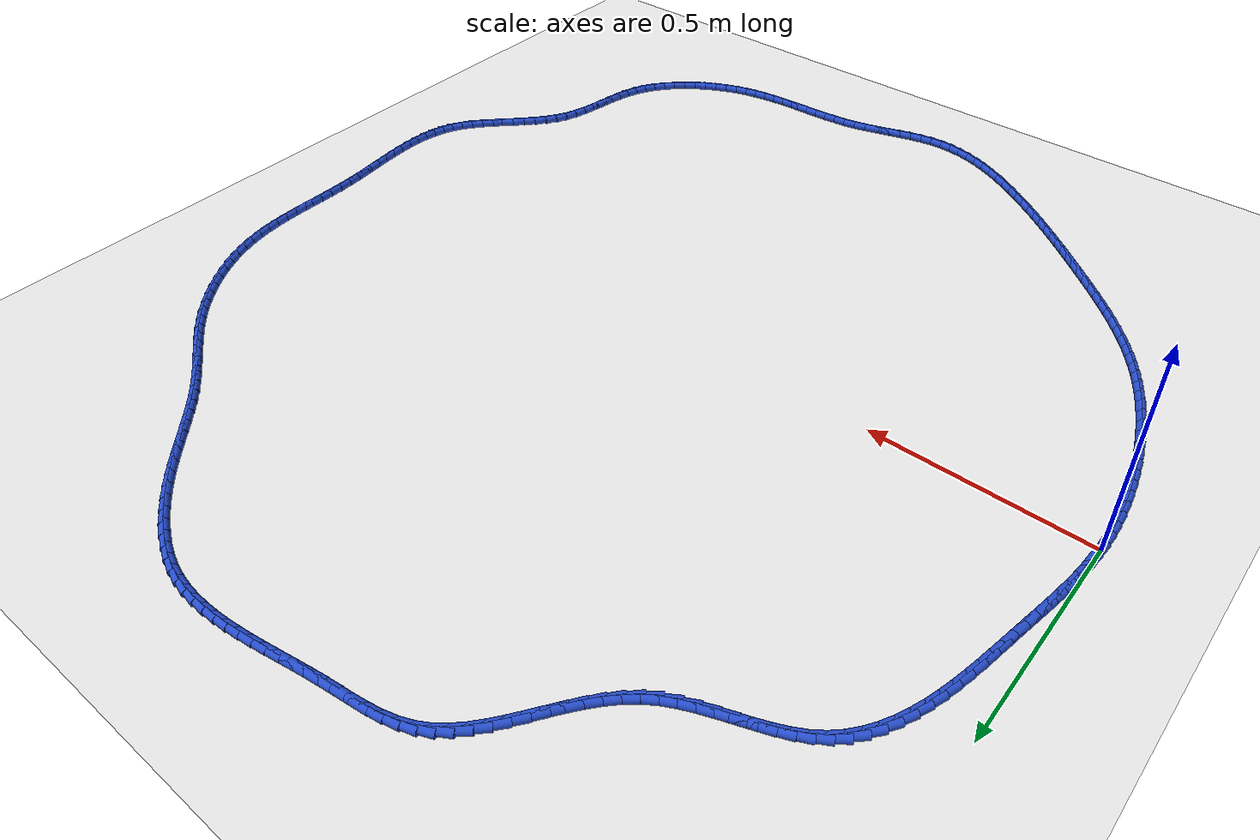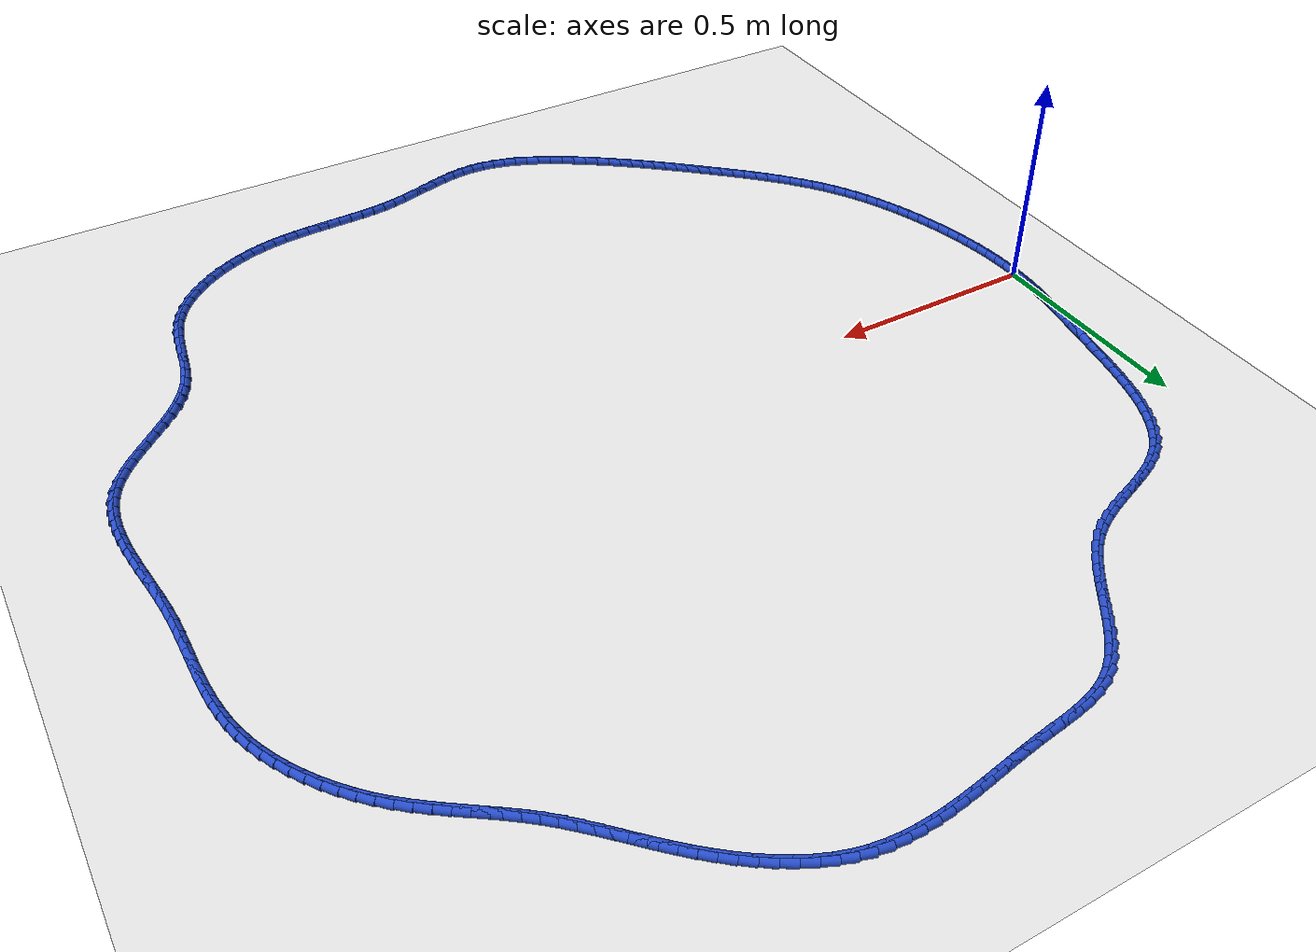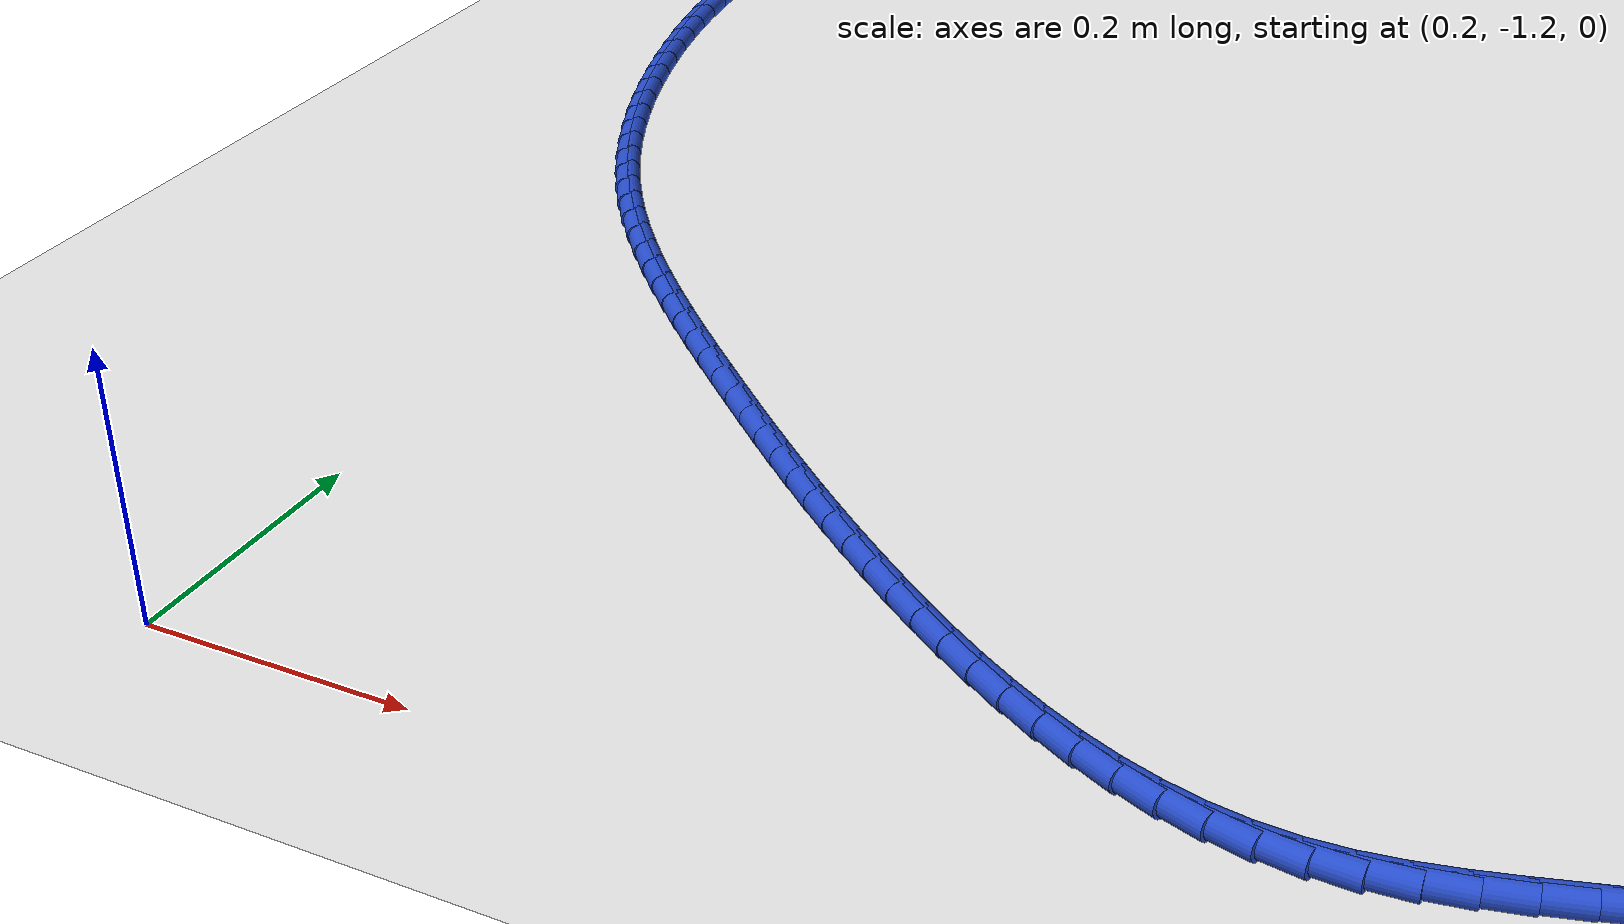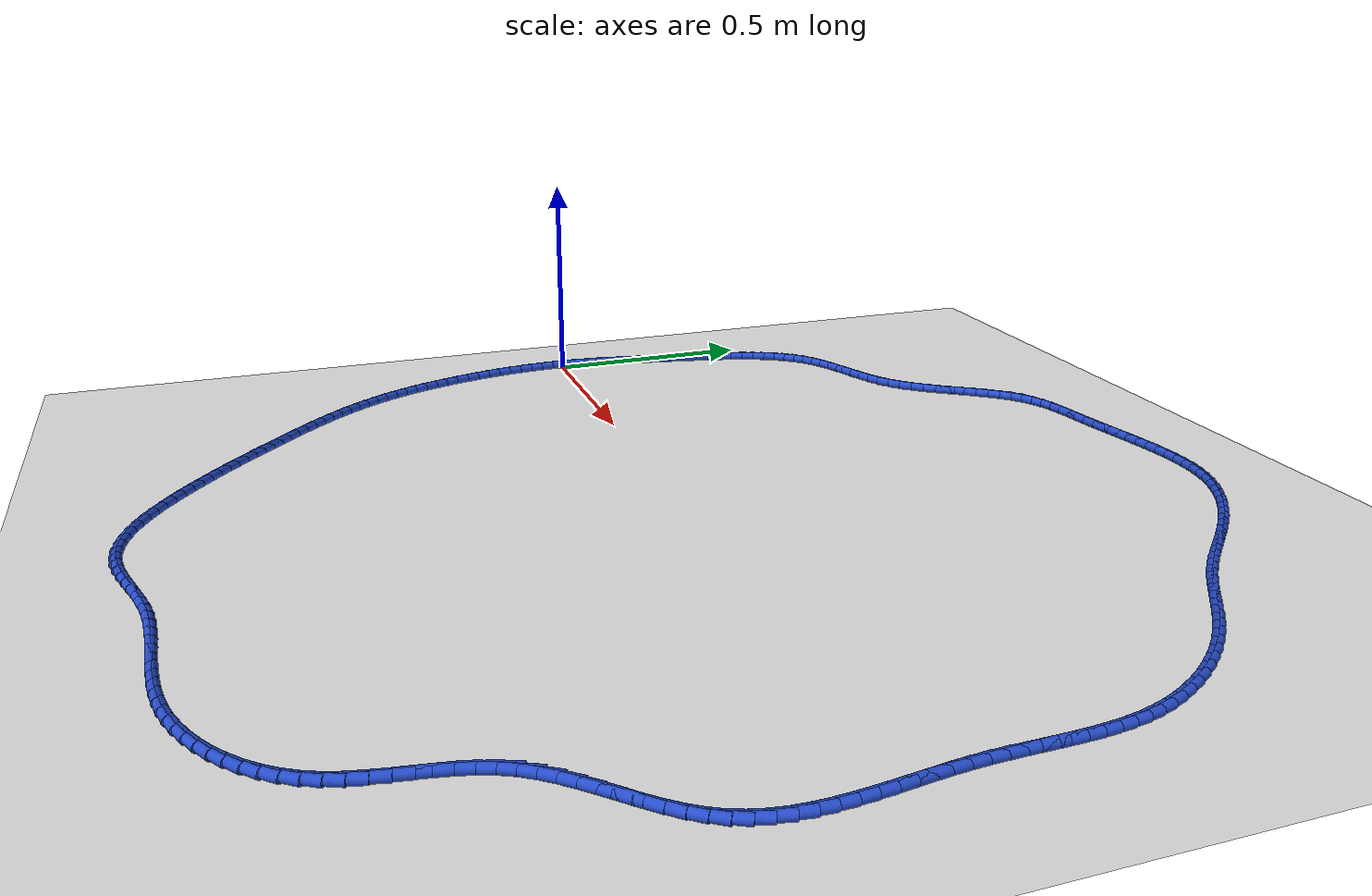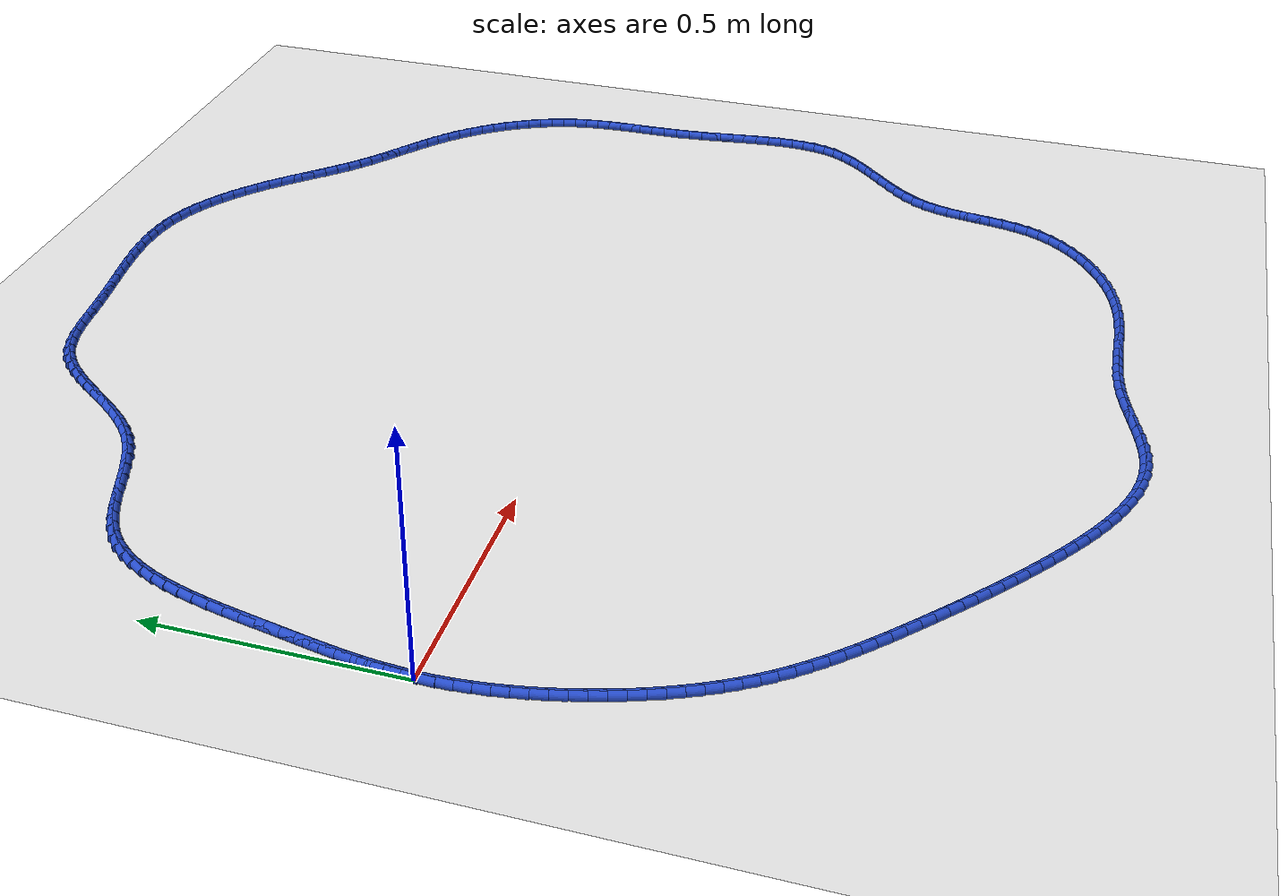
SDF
<sdf version="1.6">
 <world name="default">
  <light name="sun" type="directional">
   <pose>0 0 10 0 -0 0</pose>
   <diffuse>0.8 0.8 0.8 1</diffuse>
   <specular>0.2 0.2 0.2 1</specular>
   <attenuation>
    <range>1000</range>
    <constant>0.9</constant>
    <linear>0.01</linear>
    <quadratic>0.001</quadratic>
   </attenuation>
   <direction>-0.5 0.1 -0.9</direction>
  </light>
  <model name="ground_plane">
   <static>1</static>
   <link name="link">
    <collision name="collision">
     <geometry><plane><normal>0 0 1</normal><size>100 100</size></plane></geometry>
     <surface><friction><ode><mu>100</mu><mu2>50</mu2></ode></friction></surface>
    </collision>
    <visual name="visual">
     <cast_shadows>0</cast_shadows>
     <geometry><plane><normal>0 0 1</normal><size>100 100</size></plane></geometry>
     <material>
      <script><uri>file://media/materials/scripts/gazebo.material</uri><name>Gazebo/WhiteGlow</name></script>
     </material>
    </visual>
   </link>
  </model>
  <gravity>0 0 -9.8</gravity>
  <magnetic_field>6e-06 2.3e-05 -4.2e-05</magnetic_field>
  <atmosphere type="adiabatic"/>
  <physics name="default_physics" default="0" type="ode">
   <max_step_size>0.001</max_step_size>
   <real_time_factor>1</real_time_factor>
   <real_time_update_rate>1000</real_time_update_rate>
  </physics>
  <scene><ambient>0.4 0.4 0.4 1</ambient><background>0.7 0.7 0.7 1</background><shadows>1</shadows></scene>
  <spherical_coordinates>
   <surface_model>EARTH_WGS84</surface_model>
   <latitude_deg>0</latitude_deg>
   <longitude_deg>0</longitude_deg>
   <elevation>0</elevation>
   <heading_deg>0</heading_deg>
  </spherical_coordinates>
  <model name="line">
   <link name="link_0">
    <pose>-6.938893903907228e-18 4.163336342344337e-17 0.01 0 1.57 1.5301401341915055</pose>
    <collision name="collision">
     <geometry><cylinder><radius>0.01</radius><length>0.08</length></cylinder></geometry>
    </collision>
    <visual name="visual">
     <material>
      <script><name>Gazebo/Blue</name><uri>file://media/materials/scripts/gazebo.material</uri></script>
     </material>
     <geometry><cylinder><radius>0.01</radius><length>0.08</length></cylinder></geometry>
    </visual>
   </link>
   <link name="link_1">
    <pose>0.0012197291656639655 0.029984535512374955 0.01 0 1.57 1.4936520319378765</pose>
    <collision name="collision">
     <geometry><cylinder><radius>0.01</radius><length>0.08</length></cylinder></geometry>
    </collision>
    <visual name="visual">
     <material>
      <script><name>Gazebo/Blue</name><uri>file://media/materials/scripts/gazebo.material</uri></script>
     </material>
     <geometry><cylinder><radius>0.01</radius><length>0.08</length></cylinder></geometry>
    </visual>
   </link>
   <link name="link_2">
    <pose>0.0035273743602338486 0.059838533094403935 0.01 0 1.57 1.461882396757842</pose>
    <collision name="collision">
     <geometry><cylinder><radius>0.01</radius><length>0.08</length></cylinder></geometry>
    </collision>
    <visual name="visual">
     <material>
      <script><name>Gazebo/Blue</name><uri>file://media/materials/scripts/gazebo.material</uri></script>
     </material>
     <geometry><cylinder><radius>0.01</radius><length>0.08</length></cylinder></geometry>
    </visual>
   </link>
   <link name="link_3">
    <pose>0.006787235103199352 0.08965070479935273 0.01 0 1.57 1.4351145404454468</pose>
    <collision name="collision">
     <geometry><cylinder><radius>0.01</radius><length>0.08</length></cylinder></geometry>
    </collision>
    <visual name="visual">
     <material>
      <script><name>Gazebo/Blue</name><uri>file://media/materials/scripts/gazebo.material</uri></script>
     </material>
     <geometry><cylinder><radius>0.01</radius><length>0.08</length></cylinder></geometry>
    </visual>
   </link>
   <link name="link_4">
    <pose>0.010863610914050189 0.11950976268048714 0.01 0 1.57 1.4135051827415441</pose>
    <collision name="collision">
     <geometry><cylinder><radius>0.01</radius><length>0.08</length></cylinder></geometry>
    </collision>
    <visual name="visual">
     <material>
      <script><name>Gazebo/Blue</name><uri>file://media/materials/scripts/gazebo.material</uri></script>
     </material>
     <geometry><cylinder><radius>0.01</radius><length>0.08</length></cylinder></geometry>
    </visual>
   </link>
   <link name="link_5">
    <pose>0.015620801312276082 0.14950441879107293 0.01 0 1.57 1.3971016461890813</pose>
    <collision name="collision">
     <geometry><cylinder><radius>0.01</radius><length>0.08</length></cylinder></geometry>
    </collision>
    <visual name="visual">
     <material>
      <script><name>Gazebo/Blue</name><uri>file://media/materials/scripts/gazebo.material</uri></script>
     </material>
     <geometry><cylinder><radius>0.01</radius><length>0.08</length></cylinder></geometry>
    </visual>
   </link>
   <link name="link_6">
    <pose>0.020923105817366727 0.17972338518437583 0.01 0 1.57 1.3858606724988032</pose>
    <collision name="collision">
     <geometry><cylinder><radius>0.01</radius><length>0.08</length></cylinder></geometry>
    </collision>
    <visual name="visual">
     <material>
      <script><name>Gazebo/Blue</name><uri>file://media/materials/scripts/gazebo.material</uri></script>
     </material>
     <geometry><cylinder><radius>0.01</radius><length>0.08</length></cylinder></geometry>
    </visual>
   </link>
   <link name="link_7">
    <pose>0.02663482394881185 0.21025537391366161 0.01 0 1.57 1.3796661152563492</pose>
    <collision name="collision">
     <geometry><cylinder><radius>0.01</radius><length>0.08</length></cylinder></geometry>
    </collision>
    <visual name="visual">
     <material>
      <script><name>Gazebo/Blue</name><uri>file://media/materials/scripts/gazebo.material</uri></script>
     </material>
     <geometry><cylinder><radius>0.01</radius><length>0.08</length></cylinder></geometry>
    </visual>
   </link>
   <link name="link_8">
    <pose>0.03262025522610116 0.24118909703219615 0.01 0 1.57 1.3783439307562038</pose>
    <collision name="collision">
     <geometry><cylinder><radius>0.01</radius><length>0.08</length></cylinder></geometry>
    </collision>
    <visual name="visual">
     <material>
      <script><name>Gazebo/Blue</name><uri>file://media/materials/scripts/gazebo.material</uri></script>
     </material>
     <geometry><cylinder><radius>0.01</radius><length>0.08</length></cylinder></geometry>
    </visual>
   </link>
   <link name="link_9">
    <pose>0.038743699168724374 0.27261326659324514 0.01 0 1.57 1.3809345792185361</pose>
    <collision name="collision">
     <geometry><cylinder><radius>0.01</radius><length>0.08</length></cylinder></geometry>
    </collision>
    <visual name="visual">
     <material>
      <script><name>Gazebo/Blue</name><uri>file://media/materials/scripts/gazebo.material</uri></script>
     </material>
     <geometry><cylinder><radius>0.01</radius><length>0.08</length></cylinder></geometry>
    </visual>
   </link>
   <link name="link_10">
    <pose>0.04488989903704771 0.304595328160182 0.01 0 1.57 1.3800619963508682</pose>
    <collision name="collision">
     <geometry><cylinder><radius>0.01</radius><length>0.08</length></cylinder></geometry>
    </collision>
    <visual name="visual">
     <material>
      <script><name>Gazebo/Blue</name><uri>file://media/materials/scripts/gazebo.material</uri></script>
     </material>
     <geometry><cylinder><radius>0.01</radius><length>0.08</length></cylinder></geometry>
    </visual>
   </link>
   <link name="link_11">
    <pose>0.051145275253468625 0.33699293372906 0.01 0 1.57 1.3717603807942091</pose>
    <collision name="collision">
     <geometry><cylinder><radius>0.01</radius><length>0.08</length></cylinder></geometry>
    </collision>
    <visual name="visual">
     <material>
      <script><name>Gazebo/Blue</name><uri>file://media/materials/scripts/gazebo.material</uri></script>
     </material>
     <geometry><cylinder><radius>0.01</radius><length>0.08</length></cylinder></geometry>
    </visual>
   </link>
   <link name="link_12">
    <pose>0.057711093119129815 0.3695442685374868 0.01 0 1.57 1.3559623379499974</pose>
    <collision name="collision">
     <geometry><cylinder><radius>0.01</radius><length>0.08</length></cylinder></geometry>
    </collision>
    <visual name="visual">
     <material>
      <script><name>Gazebo/Blue</name><uri>file://media/materials/scripts/gazebo.material</uri></script>
     </material>
     <geometry><cylinder><radius>0.01</radius><length>0.08</length></cylinder></geometry>
    </visual>
   </link>
   <link name="link_13">
    <pose>0.06478994972328184 0.40198613243775777 0.01 0 1.57 1.33236724914427</pose>
    <collision name="collision">
     <geometry><cylinder><radius>0.01</radius><length>0.08</length></cylinder></geometry>
    </collision>
    <visual name="visual">
     <material>
      <script><name>Gazebo/Blue</name><uri>file://media/materials/scripts/gazebo.material</uri></script>
     </material>
     <geometry><cylinder><radius>0.01</radius><length>0.08</length></cylinder></geometry>
    </visual>
   </link>
   <link name="link_14">
    <pose>0.07258444215517523 0.4340553252821681 0.01 0 1.57 1.3004034182927375</pose>
    <collision name="collision">
     <geometry><cylinder><radius>0.01</radius><length>0.08</length></cylinder></geometry>
    </collision>
    <visual name="visual">
     <material>
      <script><name>Gazebo/Blue</name><uri>file://media/materials/scripts/gazebo.material</uri></script>
     </material>
     <geometry><cylinder><radius>0.01</radius><length>0.08</length></cylinder></geometry>
    </visual>
   </link>
   <link name="link_15">
    <pose>0.08129716750406062 0.4654886469230136 0.01 0 1.57 1.2592349097399569</pose>
    <collision name="collision">
     <geometry><cylinder><radius>0.01</radius><length>0.08</length></cylinder></geometry>
    </collision>
    <visual name="visual">
     <material>
      <script><name>Gazebo/Blue</name><uri>file://media/materials/scripts/gazebo.material</uri></script>
     </material>
     <geometry><cylinder><radius>0.01</radius><length>0.08</length></cylinder></geometry>
    </visual>
   </link>
   <link name="link_16">
    <pose>0.09113072285918855 0.4960228972125896 0.01 0 1.57 1.2077793161824977</pose>
    <collision name="collision">
     <geometry><cylinder><radius>0.01</radius><length>0.08</length></cylinder></geometry>
    </collision>
    <visual name="visual">
     <material>
      <script><name>Gazebo/Blue</name><uri>file://media/materials/scripts/gazebo.material</uri></script>
     </material>
     <geometry><cylinder><radius>0.01</radius><length>0.08</length></cylinder></geometry>
    </visual>
   </link>
   <link name="link_17">
    <pose>0.1022877053098096 0.5253948760031913 0.01 0 1.57 1.1447606539366348</pose>
    <collision name="collision">
     <geometry><cylinder><radius>0.01</radius><length>0.08</length></cylinder></geometry>
    </collision>
    <visual name="visual">
     <material>
      <script><name>Gazebo/Blue</name><uri>file://media/materials/scripts/gazebo.material</uri></script>
     </material>
     <geometry><cylinder><radius>0.01</radius><length>0.08</length></cylinder></geometry>
    </visual>
   </link>
   <link name="link_18">
    <pose>0.11497071194517433 0.5533413831471145 0.01 0 1.57 1.0688360236999108</pose>
    <collision name="collision">
     <geometry><cylinder><radius>0.01</radius><length>0.08</length></cylinder></geometry>
    </collision>
    <visual name="visual">
     <material>
      <script><name>Gazebo/Blue</name><uri>file://media/materials/scripts/gazebo.material</uri></script>
     </material>
     <geometry><cylinder><radius>0.01</radius><length>0.08</length></cylinder></geometry>
    </visual>
   </link>
   <link name="link_19">
    <pose>0.12938233985453332 0.5795992184966544 0.01 0 1.57 0.9788486881386602</pose>
    <collision name="collision">
     <geometry><cylinder><radius>0.01</radius><length>0.08</length></cylinder></geometry>
    </collision>
    <visual name="visual">
     <material>
      <script><name>Gazebo/Blue</name><uri>file://media/materials/scripts/gazebo.material</uri></script>
     </material>
     <geometry><cylinder><radius>0.01</radius><length>0.08</length></cylinder></geometry>
    </visual>
   </link>
   <link name="link_20">
    <pose>0.14572518612713709 0.6039051819041062 0.01 0 1.57 0.8742551975104315</pose>
    <collision name="collision">
     <geometry><cylinder><radius>0.01</radius><length>0.08</length></cylinder></geometry>
    </collision>
    <visual name="visual">
     <material>
      <script><name>Gazebo/Blue</name><uri>file://media/materials/scripts/gazebo.material</uri></script>
     </material>
     <geometry><cylinder><radius>0.01</radius><length>0.08</length></cylinder></geometry>
    </visual>
   </link>
   <link name="link_21">
    <pose>0.1642018478522362 0.6259960732217655 0.01 0 1.57 0.7557115355493477</pose>
    <collision name="collision">
     <geometry><cylinder><radius>0.01</radius><length>0.08</length></cylinder></geometry>
    </collision>
    <visual name="visual">
     <material>
      <script><name>Gazebo/Blue</name><uri>file://media/materials/scripts/gazebo.material</uri></script>
     </material>
     <geometry><cylinder><radius>0.01</radius><length>0.08</length></cylinder></geometry>
    </visual>
   </link>
   <link name="link_22">
    <pose>0.1850149221190814 0.6456086923019283 0.01 0 1.57 0.6275920889381426</pose>
    <collision name="collision">
     <geometry><cylinder><radius>0.01</radius><length>0.08</length></cylinder></geometry>
    </collision>
    <visual name="visual">
     <material>
      <script><name>Gazebo/Blue</name><uri>file://media/materials/scripts/gazebo.material</uri></script>
     </material>
     <geometry><cylinder><radius>0.01</radius><length>0.08</length></cylinder></geometry>
    </visual>
   </link>
   <link name="link_23">
    <pose>0.20833172702468405 0.6625234769087504 0.01 0 1.57 0.5156470011556986</pose>
    <collision name="collision">
     <geometry><cylinder><radius>0.01</radius><length>0.08</length></cylinder></geometry>
    </collision>
    <visual name="visual">
     <material>
      <script><name>Gazebo/Blue</name><uri>file://media/materials/scripts/gazebo.material</uri></script>
     </material>
     <geometry><cylinder><radius>0.01</radius><length>0.08</length></cylinder></geometry>
    </visual>
   </link>
   <link name="link_24">
    <pose>0.2339135190198037 0.6770231377230682 0.01 0 1.57 0.4344191377419434</pose>
    <collision name="collision">
     <geometry><cylinder><radius>0.01</radius><length>0.08</length></cylinder></geometry>
    </collision>
    <visual name="visual">
     <material>
      <script><name>Gazebo/Blue</name><uri>file://media/materials/scripts/gazebo.material</uri></script>
     </material>
     <geometry><cylinder><radius>0.01</radius><length>0.08</length></cylinder></geometry>
    </visual>
   </link>
   <link name="link_25">
    <pose>0.2612614927718114 0.6897120656229611 0.01 0 1.57 0.38181340397320773</pose>
    <collision name="collision">
     <geometry><cylinder><radius>0.01</radius><length>0.08</length></cylinder></geometry>
    </collision>
    <visual name="visual">
     <material>
      <script><name>Gazebo/Blue</name><uri>file://media/materials/scripts/gazebo.material</uri></script>
     </material>
     <geometry><cylinder><radius>0.01</radius><length>0.08</length></cylinder></geometry>
    </visual>
   </link>
   <link name="link_26">
    <pose>0.2898725937474145 0.7011999074825637 0.01 0 1.57 0.3552501573249318</pose>
    <collision name="collision">
     <geometry><cylinder><radius>0.01</radius><length>0.08</length></cylinder></geometry>
    </collision>
    <visual name="visual">
     <material>
      <script><name>Gazebo/Blue</name><uri>file://media/materials/scripts/gazebo.material</uri></script>
     </material>
     <geometry><cylinder><radius>0.01</radius><length>0.08</length></cylinder></geometry>
    </visual>
   </link>
   <link name="link_27">
    <pose>0.3192437674133202 0.7120963101760102 0.01 0 1.57 0.35295950410676824</pose>
    <collision name="collision">
     <geometry><cylinder><radius>0.01</radius><length>0.08</length></cylinder></geometry>
    </collision>
    <visual name="visual">
     <material>
      <script><name>Gazebo/Blue</name><uri>file://media/materials/scripts/gazebo.material</uri></script>
     </material>
     <geometry><cylinder><radius>0.01</radius><length>0.08</length></cylinder></geometry>
    </visual>
   </link>
   <link name="link_28">
    <pose>0.34887195923623615 0.7230109205774358 0.01 0 1.57 0.3743181470414608</pose>
    <collision name="collision">
     <geometry><cylinder><radius>0.01</radius><length>0.08</length></cylinder></geometry>
    </collision>
    <visual name="visual">
     <material>
      <script><name>Gazebo/Blue</name><uri>file://media/materials/scripts/gazebo.material</uri></script>
     </material>
     <geometry><cylinder><radius>0.01</radius><length>0.08</length></cylinder></geometry>
    </visual>
   </link>
   <link name="link_29">
    <pose>0.3782541146828697 0.7345533855609746 0.01 0 1.57 0.4198027358850559</pose>
    <collision name="collision">
     <geometry><cylinder><radius>0.01</radius><length>0.08</length></cylinder></geometry>
    </collision>
    <visual name="visual">
     <material>
      <script><name>Gazebo/Blue</name><uri>file://media/materials/scripts/gazebo.material</uri></script>
     </material>
     <geometry><cylinder><radius>0.01</radius><length>0.08</length></cylinder></geometry>
    </visual>
   </link>
   <link name="link_30">
    <pose>0.406887179219928 0.7473333520007615 0.01 0 1.57 0.4906382961884861</pose>
    <collision name="collision">
     <geometry><cylinder><radius>0.01</radius><length>0.08</length></cylinder></geometry>
    </collision>
    <visual name="visual">
     <material>
      <script><name>Gazebo/Blue</name><uri>file://media/materials/scripts/gazebo.material</uri></script>
     </material>
     <geometry><cylinder><radius>0.01</radius><length>0.08</length></cylinder></geometry>
    </visual>
   </link>
   <link name="link_31">
    <pose>0.4342680983141185 0.7619604667709305 0.01 0 1.57 0.587996325562744</pose>
    <collision name="collision">
     <geometry><cylinder><radius>0.01</radius><length>0.08</length></cylinder></geometry>
    </collision>
    <visual name="visual">
     <material>
      <script><name>Gazebo/Blue</name><uri>file://media/materials/scripts/gazebo.material</uri></script>
     </material>
     <geometry><cylinder><radius>0.01</radius><length>0.08</length></cylinder></geometry>
    </visual>
   </link>
   <link name="link_32">
    <pose>0.4598939819887914 0.779044156841039 0.01 0 1.57 0.7009229676844824</pose>
    <collision name="collision">
     <geometry><cylinder><radius>0.01</radius><length>0.08</length></cylinder></geometry>
    </collision>
    <visual name="visual">
     <material>
      <script><name>Gazebo/Blue</name><uri>file://media/materials/scripts/gazebo.material</uri></script>
     </material>
     <geometry><cylinder><radius>0.01</radius><length>0.08</length></cylinder></geometry>
    </visual>
   </link>
   <link name="link_33">
    <pose>0.48345927634729785 0.7989301399389541 0.01 0 1.57 0.7962964450090528</pose>
    <collision name="collision">
     <geometry><cylinder><radius>0.01</radius><length>0.08</length></cylinder></geometry>
    </collision>
    <visual name="visual">
     <material>
      <script><name>Gazebo/Blue</name><uri>file://media/materials/scripts/gazebo.material</uri></script>
     </material>
     <geometry><cylinder><radius>0.01</radius><length>0.08</length></cylinder></geometry>
    </visual>
   </link>
   <link name="link_34">
    <pose>0.5052383434325876 0.8211891655623366 0.01 0 1.57 0.8682069815176386</pose>
    <collision name="collision">
     <geometry><cylinder><radius>0.01</radius><length>0.08</length></cylinder></geometry>
    </collision>
    <visual name="visual">
     <material>
      <script><name>Gazebo/Blue</name><uri>file://media/materials/scripts/gazebo.material</uri></script>
     </material>
     <geometry><cylinder><radius>0.01</radius><length>0.08</length></cylinder></geometry>
    </visual>
   </link>
   <link name="link_35">
    <pose>0.5256115331539314 0.8452503467688447 0.01 0 1.57 0.9177906173250896</pose>
    <collision name="collision">
     <geometry><cylinder><radius>0.01</radius><length>0.08</length></cylinder></geometry>
    </collision>
    <visual name="visual">
     <material>
      <script><name>Gazebo/Blue</name><uri>file://media/materials/scripts/gazebo.material</uri></script>
     </material>
     <geometry><cylinder><radius>0.01</radius><length>0.08</length></cylinder></geometry>
    </visual>
   </link>
   <link name="link_36">
    <pose>0.5449591954205995 0.8705427966161362 0.01 0 1.57 0.9463560596398295</pose>
    <collision name="collision">
     <geometry><cylinder><radius>0.01</radius><length>0.08</length></cylinder></geometry>
    </collision>
    <visual name="visual">
     <material>
      <script><name>Gazebo/Blue</name><uri>file://media/materials/scripts/gazebo.material</uri></script>
     </material>
     <geometry><cylinder><radius>0.01</radius><length>0.08</length></cylinder></geometry>
    </visual>
   </link>
   <link name="link_37">
    <pose>0.5636616801418621 0.896495628161869 0.01 0 1.57 0.95472931715663</pose>
    <collision name="collision">
     <geometry><cylinder><radius>0.01</radius><length>0.08</length></cylinder></geometry>
    </collision>
    <visual name="visual">
     <material>
      <script><name>Gazebo/Blue</name><uri>file://media/materials/scripts/gazebo.material</uri></script>
     </material>
     <geometry><cylinder><radius>0.01</radius><length>0.08</length></cylinder></geometry>
    </visual>
   </link>
   <link name="link_38">
    <pose>0.5820993372269899 0.9225379544637006 0.01 0 1.57 0.9429369674868294</pose>
    <collision name="collision">
     <geometry><cylinder><radius>0.01</radius><length>0.08</length></cylinder></geometry>
    </collision>
    <visual name="visual">
     <material>
      <script><name>Gazebo/Blue</name><uri>file://media/materials/scripts/gazebo.material</uri></script>
     </material>
     <geometry><cylinder><radius>0.01</radius><length>0.08</length></cylinder></geometry>
    </visual>
   </link>
   <link name="link_39">
    <pose>0.6006525165852534 0.9480988885792894 0.01 0 1.57 0.9100897329212555</pose>
    <collision name="collision">
     <geometry><cylinder><radius>0.01</radius><length>0.08</length></cylinder></geometry>
    </collision>
    <visual name="visual">
     <material>
      <script><name>Gazebo/Blue</name><uri>file://media/materials/scripts/gazebo.material</uri></script>
     </material>
     <geometry><cylinder><radius>0.01</radius><length>0.08</length></cylinder></geometry>
    </visual>
   </link>
   <link name="link_40">
    <pose>0.6197015681259226 0.9726075435662926 0.01 0 1.57 0.8544347972120412</pose>
    <collision name="collision">
     <geometry><cylinder><radius>0.01</radius><length>0.08</length></cylinder></geometry>
    </collision>
    <visual name="visual">
     <material>
      <script><name>Gazebo/Blue</name><uri>file://media/materials/scripts/gazebo.material</uri></script>
     </material>
     <geometry><cylinder><radius>0.01</radius><length>0.08</length></cylinder></geometry>
    </visual>
   </link>
   <link name="link_41">
    <pose>0.6396268417582678 0.9954930324823682 0.01 0 1.57 0.7736869410631354</pose>
    <collision name="collision">
     <geometry><cylinder><radius>0.01</radius><length>0.08</length></cylinder></geometry>
    </collision>
    <visual name="visual">
     <material>
      <script><name>Gazebo/Blue</name><uri>file://media/materials/scripts/gazebo.material</uri></script>
     </material>
     <geometry><cylinder><radius>0.01</radius><length>0.08</length></cylinder></geometry>
    </visual>
   </link>
   <link name="link_42">
    <pose>0.66080868739156 1.0161844683851746 0.01 0 1.57 0.6659005265900584</pose>
    <collision name="collision">
     <geometry><cylinder><radius>0.01</radius><length>0.08</length></cylinder></geometry>
    </collision>
    <visual name="visual">
     <material>
      <script><name>Gazebo/Blue</name><uri>file://media/materials/scripts/gazebo.material</uri></script>
     </material>
     <geometry><cylinder><radius>0.01</radius><length>0.08</length></cylinder></geometry>
    </visual>
   </link>
   <link name="link_43">
    <pose>0.6836274549350689 1.0341109643323692 0.01 0 1.57 0.5314114012457416</pose>
    <collision name="collision">
     <geometry><cylinder><radius>0.01</radius><length>0.08</length></cylinder></geometry>
    </collision>
    <visual name="visual">
     <material>
      <script><name>Gazebo/Blue</name><uri>file://media/materials/scripts/gazebo.material</uri></script>
     </material>
     <geometry><cylinder><radius>0.01</radius><length>0.08</length></cylinder></geometry>
    </visual>
   </link>
   <link name="link_44">
    <pose>0.7084598205210532 1.0487077893040606 0.01 0 1.57 0.3924067201322256</pose>
    <collision name="collision">
     <geometry><cylinder><radius>0.01</radius><length>0.08</length></cylinder></geometry>
    </collision>
    <visual name="visual">
     <material>
      <script><name>Gazebo/Blue</name><uri>file://media/materials/scripts/gazebo.material</uri></script>
     </material>
     <geometry><cylinder><radius>0.01</radius><length>0.08</length></cylinder></geometry>
    </visual>
   </link>
   <link name="link_45">
    <pose>0.7354124254588414 1.0598626930442647 0.01 0 1.57 0.28299546709065515</pose>
    <collision name="collision">
     <geometry><cylinder><radius>0.01</radius><length>0.08</length></cylinder></geometry>
    </collision>
    <visual name="visual">
     <material>
      <script><name>Gazebo/Blue</name><uri>file://media/materials/scripts/gazebo.material</uri></script>
     </material>
     <geometry><cylinder><radius>0.01</radius><length>0.08</length></cylinder></geometry>
    </visual>
   </link>
   <link name="link_46">
    <pose>0.7641420264823895 1.0682172692424816 0.01 0 1.57 0.20514347542160874</pose>
    <collision name="collision">
     <geometry><cylinder><radius>0.01</radius><length>0.08</length></cylinder></geometry>
    </collision>
    <visual name="visual">
     <material>
      <script><name>Gazebo/Blue</name><uri>file://media/materials/scripts/gazebo.material</uri></script>
     </material>
     <geometry><cylinder><radius>0.01</radius><length>0.08</length></cylinder></geometry>
    </visual>
   </link>
   <link name="link_47">
    <pose>0.7942627719635992 1.0744845078029719 0.01 0 1.57 0.15592012926868903</pose>
    <collision name="collision">
     <geometry><cylinder><radius>0.01</radius><length>0.08</length></cylinder></geometry>
    </collision>
    <visual name="visual">
     <material>
      <script><name>Gazebo/Blue</name><uri>file://media/materials/scripts/gazebo.material</uri></script>
     </material>
     <geometry><cylinder><radius>0.01</radius><length>0.08</length></cylinder></geometry>
    </visual>
   </link>
   <link name="link_48">
    <pose>0.8253888102743729 1.0793773986299975 0.01 0 1.57 0.13251446589228144</pose>
    <collision name="collision">
     <geometry><cylinder><radius>0.01</radius><length>0.08</length></cylinder></geometry>
    </collision>
    <visual name="visual">
     <material>
      <script><name>Gazebo/Blue</name><uri>file://media/materials/scripts/gazebo.material</uri></script>
     </material>
     <geometry><cylinder><radius>0.01</radius><length>0.08</length></cylinder></geometry>
    </visual>
   </link>
   <link name="link_49">
    <pose>0.8571342897866128 1.0836089316278192 0.01 0 1.57 0.13314166170793224</pose>
    <collision name="collision">
     <geometry><cylinder><radius>0.01</radius><length>0.08</length></cylinder></geometry>
    </collision>
    <visual name="visual">
     <material>
      <script><name>Gazebo/Blue</name><uri>file://media/materials/scripts/gazebo.material</uri></script>
     </material>
     <geometry><cylinder><radius>0.01</radius><length>0.08</length></cylinder></geometry>
    </visual>
   </link>
   <link name="link_50">
    <pose>0.8891133874812078 1.087892020138957 0.01 0 1.57 0.15070542576389961</pose>
    <collision name="collision">
     <geometry><cylinder><radius>0.01</radius><length>0.08</length></cylinder></geometry>
    </collision>
    <visual name="visual">
     <material>
      <script><name>Gazebo/Blue</name><uri>file://media/materials/scripts/gazebo.material</uri></script>
     </material>
     <geometry><cylinder><radius>0.01</radius><length>0.08</length></cylinder></geometry>
    </visual>
   </link>
   <link name="link_51">
    <pose>0.9210161028964097 1.092736665501395 0.01 0 1.57 0.16453330855834616</pose>
    <collision name="collision">
     <geometry><cylinder><radius>0.01</radius><length>0.08</length></cylinder></geometry>
    </collision>
    <visual name="visual">
     <material>
      <script><name>Gazebo/Blue</name><uri>file://media/materials/scripts/gazebo.material</uri></script>
     </material>
     <geometry><cylinder><radius>0.01</radius><length>0.08</length></cylinder></geometry>
    </visual>
   </link>
   <link name="link_52">
    <pose>0.9527728893615699 1.0980093803282718 0.01 0 1.57 0.17054085145520473</pose>
    <collision name="collision">
     <geometry><cylinder><radius>0.01</radius><length>0.08</length></cylinder></geometry>
    </collision>
    <visual name="visual">
     <material>
      <script><name>Gazebo/Blue</name><uri>file://media/materials/scripts/gazebo.material</uri></script>
     </material>
     <geometry><cylinder><radius>0.01</radius><length>0.08</length></cylinder></geometry>
    </visual>
   </link>
   <link name="link_53">
    <pose>0.984361754733883 1.1034494145169185 0.01 0 1.57 0.16866196655547902</pose>
    <collision name="collision">
     <geometry><cylinder><radius>0.01</radius><length>0.08</length></cylinder></geometry>
    </collision>
    <visual name="visual">
     <material>
      <script><name>Gazebo/Blue</name><uri>file://media/materials/scripts/gazebo.material</uri></script>
     </material>
     <geometry><cylinder><radius>0.01</radius><length>0.08</length></cylinder></geometry>
    </visual>
   </link>
   <link name="link_54">
    <pose>1.015760706870543 1.1087960179646674 0.01 0 1.57 0.15873326930780768</pose>
    <collision name="collision">
     <geometry><cylinder><radius>0.01</radius><length>0.08</length></cylinder></geometry>
    </collision>
    <visual name="visual">
     <material>
      <script><name>Gazebo/Blue</name><uri>file://media/materials/scripts/gazebo.material</uri></script>
     </material>
     <geometry><cylinder><radius>0.01</radius><length>0.08</length></cylinder></geometry>
    </visual>
   </link>
   <link name="link_55">
    <pose>1.0469477536287444 1.11378844056885 0.01 0 1.57 0.14049145370652116</pose>
    <collision name="collision">
     <geometry><cylinder><radius>0.01</radius><length>0.08</length></cylinder></geometry>
    </collision>
    <visual name="visual">
     <material>
      <script><name>Gazebo/Blue</name><uri>file://media/materials/scripts/gazebo.material</uri></script>
     </material>
     <geometry><cylinder><radius>0.01</radius><length>0.08</length></cylinder></geometry>
    </visual>
   </link>
   <link name="link_56">
    <pose>1.0779009028656812 1.1181659322267992 0.01 0 1.57 0.11358467103288736</pose>
    <collision name="collision">
     <geometry><cylinder><radius>0.01</radius><length>0.08</length></cylinder></geometry>
    </collision>
    <visual name="visual">
     <material>
      <script><name>Gazebo/Blue</name><uri>file://media/materials/scripts/gazebo.material</uri></script>
     </material>
     <geometry><cylinder><radius>0.01</radius><length>0.08</length></cylinder></geometry>
    </visual>
   </link>
   <link name="link_57">
    <pose>1.1085981624385484 1.1216677428358455 0.01 0 1.57 0.07760281318565207</pose>
    <collision name="collision">
     <geometry><cylinder><radius>0.01</radius><length>0.08</length></cylinder></geometry>
    </collision>
    <visual name="visual">
     <material>
      <script><name>Gazebo/Blue</name><uri>file://media/materials/scripts/gazebo.material</uri></script>
     </material>
     <geometry><cylinder><radius>0.01</radius><length>0.08</length></cylinder></geometry>
    </visual>
   </link>
   <link name="link_58">
    <pose>1.1390175402045393 1.1240331222933213 0.01 0 1.57 0.03213415901626179</pose>
    <collision name="collision">
     <geometry><cylinder><radius>0.01</radius><length>0.08</length></cylinder></geometry>
    </collision>
    <visual name="visual">
     <material>
      <script><name>Gazebo/Blue</name><uri>file://media/materials/scripts/gazebo.material</uri></script>
     </material>
     <geometry><cylinder><radius>0.01</radius><length>0.08</length></cylinder></geometry>
    </visual>
   </link>
   <link name="link_59">
    <pose>1.1691370440208488 1.1250013204965583 0.01 0 1.57 -0.023143110017349037</pose>
    <collision name="collision">
     <geometry><cylinder><radius>0.01</radius><length>0.08</length></cylinder></geometry>
    </collision>
    <visual name="visual">
     <material>
      <script><name>Gazebo/Blue</name><uri>file://media/materials/scripts/gazebo.material</uri></script>
     </material>
     <geometry><cylinder><radius>0.01</radius><length>0.08</length></cylinder></geometry>
    </visual>
   </link>
   <link name="link_60">
    <pose>1.1989346817446702 1.1243115873428884 0.01 0 1.57 -0.08832915422428958</pose>
    <collision name="collision">
     <geometry><cylinder><radius>0.01</radius><length>0.08</length></cylinder></geometry>
    </collision>
    <visual name="visual">
     <material>
      <script><name>Gazebo/Blue</name><uri>file://media/materials/scripts/gazebo.material</uri></script>
     </material>
     <geometry><cylinder><radius>0.01</radius><length>0.08</length></cylinder></geometry>
    </visual>
   </link>
   <link name="link_61">
    <pose>1.2283884612331992 1.1217031727296436 0.01 0 1.57 -0.16313629293200205</pose>
    <collision name="collision">
     <geometry><cylinder><radius>0.01</radius><length>0.08</length></cylinder></geometry>
    </collision>
    <visual name="visual">
     <material>
      <script><name>Gazebo/Blue</name><uri>file://media/materials/scripts/gazebo.material</uri></script>
     </material>
     <geometry><cylinder><radius>0.01</radius><length>0.08</length></cylinder></geometry>
    </visual>
   </link>
   <link name="link_62">
    <pose>1.257476390343629 1.1169153265541558 0.01 0 1.57 -0.24667478029076448</pose>
    <collision name="collision">
     <geometry><cylinder><radius>0.01</radius><length>0.08</length></cylinder></geometry>
    </collision>
    <visual name="visual">
     <material>
      <script><name>Gazebo/Blue</name><uri>file://media/materials/scripts/gazebo.material</uri></script>
     </material>
     <geometry><cylinder><radius>0.01</radius><length>0.08</length></cylinder></geometry>
    </visual>
   </link>
   <link name="link_63">
    <pose>1.2861763682849185 1.109688589145686 0.01 0 1.57 -0.3325190543589794</pose>
    <collision name="collision">
     <geometry><cylinder><radius>0.01</radius><length>0.08</length></cylinder></geometry>
    </collision>
    <visual name="visual">
     <material>
      <script><name>Gazebo/Blue</name><uri>file://media/materials/scripts/gazebo.material</uri></script>
     </material>
     <geometry><cylinder><radius>0.01</radius><length>0.08</length></cylinder></geometry>
    </visual>
   </link>
   <link name="link_64">
    <pose>1.3144528192418148 1.0999235457840157 0.01 0 1.57 -0.410332148560389</pose>
    <collision name="collision">
     <geometry><cylinder><radius>0.01</radius><length>0.08</length></cylinder></geometry>
    </collision>
    <visual name="visual">
     <material>
      <script><name>Gazebo/Blue</name><uri>file://media/materials/scripts/gazebo.material</uri></script>
     </material>
     <geometry><cylinder><radius>0.01</radius><length>0.08</length></cylinder></geometry>
    </visual>
   </link>
   <link name="link_65">
    <pose>1.3422438182778569 1.0878337343443036 0.01 0 1.57 -0.47951037030673416</pose>
    <collision name="collision">
     <geometry><cylinder><radius>0.01</radius><length>0.08</length></cylinder></geometry>
    </collision>
    <visual name="visual">
     <material>
      <script><name>Gazebo/Blue</name><uri>file://media/materials/scripts/gazebo.material</uri></script>
     </material>
     <geometry><cylinder><radius>0.01</radius><length>0.08</length></cylinder></geometry>
    </visual>
   </link>
   <link name="link_66">
    <pose>1.3694843880322782 1.0736689468181786 0.01 0 1.57 -0.5408301602242348</pose>
    <collision name="collision">
     <geometry><cylinder><radius>0.01</radius><length>0.08</length></cylinder></geometry>
    </collision>
    <visual name="visual">
     <material>
      <script><name>Gazebo/Blue</name><uri>file://media/materials/scripts/gazebo.material</uri></script>
     </material>
     <geometry><cylinder><radius>0.01</radius><length>0.08</length></cylinder></geometry>
    </visual>
   </link>
   <link name="link_67">
    <pose>1.3961095511443111 1.0576789751972704 0.01 0 1.57 -0.5951421493192169</pose>
    <collision name="collision">
     <geometry><cylinder><radius>0.01</radius><length>0.08</length></cylinder></geometry>
    </collision>
    <visual name="visual">
     <material>
      <script><name>Gazebo/Blue</name><uri>file://media/materials/scripts/gazebo.material</uri></script>
     </material>
     <geometry><cylinder><radius>0.01</radius><length>0.08</length></cylinder></geometry>
    </visual>
   </link>
   <link name="link_68">
    <pose>1.4220543302531885 1.040113611473207 0.01 0 1.57 -0.6432826686517489</pose>
    <collision name="collision">
     <geometry><cylinder><radius>0.01</radius><length>0.08</length></cylinder></geometry>
    </collision>
    <visual name="visual">
     <material>
      <script><name>Gazebo/Blue</name><uri>file://media/materials/scripts/gazebo.material</uri></script>
     </material>
     <geometry><cylinder><radius>0.01</radius><length>0.08</length></cylinder></geometry>
    </visual>
   </link>
   <link name="link_69">
    <pose>1.4472537479981422 1.0212226476376178 0.01 0 1.57 -0.6860259082498815</pose>
    <collision name="collision">
     <geometry><cylinder><radius>0.01</radius><length>0.08</length></cylinder></geometry>
    </collision>
    <visual name="visual">
     <material>
      <script><name>Gazebo/Blue</name><uri>file://media/materials/scripts/gazebo.material</uri></script>
     </material>
     <geometry><cylinder><radius>0.01</radius><length>0.08</length></cylinder></geometry>
    </visual>
   </link>
   <link name="link_70">
    <pose>1.4716428270184054 1.001255875682132 0.01 0 1.57 -0.7240472133193749</pose>
    <collision name="collision">
     <geometry><cylinder><radius>0.01</radius><length>0.08</length></cylinder></geometry>
    </collision>
    <visual name="visual">
     <material>
      <script><name>Gazebo/Blue</name><uri>file://media/materials/scripts/gazebo.material</uri></script>
     </material>
     <geometry><cylinder><radius>0.01</radius><length>0.08</length></cylinder></geometry>
    </visual>
   </link>
   <link name="link_71">
    <pose>1.4951575300693491 0.9804629061123997 0.01 0 1.57 -0.7563191431337096</pose>
    <collision name="collision">
     <geometry><cylinder><radius>0.01</radius><length>0.08</length></cylinder></geometry>
    </collision>
    <visual name="visual">
     <material>
      <script><name>Gazebo/Blue</name><uri>file://media/materials/scripts/gazebo.material</uri></script>
     </material>
     <geometry><cylinder><radius>0.01</radius><length>0.08</length></cylinder></geometry>
    </visual>
   </link>
   <link name="link_72">
    <pose>1.5178264443172 0.9590754686306682 0.01 0 1.57 -0.7799574278354349</pose>
    <collision name="collision">
     <geometry><cylinder><radius>0.01</radius><length>0.08</length></cylinder></geometry>
    </collision>
    <visual name="visual">
     <material>
      <script><name>Gazebo/Blue</name><uri>file://media/materials/scripts/gazebo.material</uri></script>
     </material>
     <geometry><cylinder><radius>0.01</radius><length>0.08</length></cylinder></geometry>
    </visual>
   </link>
   <link name="link_73">
    <pose>1.5398476736232185 0.9372925683618358 0.01 0 1.57 -0.7944196812804019</pose>
    <collision name="collision">
     <geometry><cylinder><radius>0.01</radius><length>0.08</length></cylinder></geometry>
    </collision>
    <visual name="visual">
     <material>
      <script><name>Gazebo/Blue</name><uri>file://media/materials/scripts/gazebo.material</uri></script>
     </material>
     <geometry><cylinder><radius>0.01</radius><length>0.08</length></cylinder></geometry>
    </visual>
   </link>
   <link name="link_74">
    <pose>1.5614374245231066 0.915309715775776 0.01 0 1.57 -0.7995298411521264</pose>
    <collision name="collision">
     <geometry><cylinder><radius>0.01</radius><length>0.08</length></cylinder></geometry>
    </collision>
    <visual name="visual">
     <material>
      <script><name>Gazebo/Blue</name><uri>file://media/materials/scripts/gazebo.material</uri></script>
     </material>
     <geometry><cylinder><radius>0.01</radius><length>0.08</length></cylinder></geometry>
    </visual>
   </link>
   <link name="link_75">
    <pose>1.582811903552567 0.8933224213423635 0.01 0 1.57 -0.7951452750269012</pose>
    <collision name="collision">
     <geometry><cylinder><radius>0.01</radius><length>0.08</length></cylinder></geometry>
    </collision>
    <visual name="visual">
     <material>
      <script><name>Gazebo/Blue</name><uri>file://media/materials/scripts/gazebo.material</uri></script>
     </material>
     <geometry><cylinder><radius>0.01</radius><length>0.08</length></cylinder></geometry>
    </visual>
   </link>
   <link name="link_76">
    <pose>1.6041873172473018 0.8715261955314718 0.01 0 1.57 -0.7811447282870082</pose>
    <collision name="collision">
     <geometry><cylinder><radius>0.01</radius><length>0.08</length></cylinder></geometry>
    </collision>
    <visual name="visual">
     <material>
      <script><name>Gazebo/Blue</name><uri>file://media/materials/scripts/gazebo.material</uri></script>
     </material>
     <geometry><cylinder><radius>0.01</radius><length>0.08</length></cylinder></geometry>
    </visual>
   </link>
   <link name="link_77">
    <pose>1.6257798721430123 0.8501165488129753 0.01 0 1.57 -0.757441651362786</pose>
    <collision name="collision">
     <geometry><cylinder><radius>0.01</radius><length>0.08</length></cylinder></geometry>
    </collision>
    <visual name="visual">
     <material>
      <script><name>Gazebo/Blue</name><uri>file://media/materials/scripts/gazebo.material</uri></script>
     </material>
     <geometry><cylinder><radius>0.01</radius><length>0.08</length></cylinder></geometry>
    </visual>
   </link>
   <link name="link_78">
    <pose>1.6478057747754016 0.8292889916567473 0.01 0 1.57 -0.7240247974301102</pose>
    <collision name="collision">
     <geometry><cylinder><radius>0.01</radius><length>0.08</length></cylinder></geometry>
    </collision>
    <visual name="visual">
     <material>
      <script><name>Gazebo/Blue</name><uri>file://media/materials/scripts/gazebo.material</uri></script>
     </material>
     <geometry><cylinder><radius>0.01</radius><length>0.08</length></cylinder></geometry>
    </visual>
   </link>
   <link name="link_79">
    <pose>1.6704812316801707 0.8092390345326625 0.01 0 1.57 -0.68355450266241</pose>
    <collision name="collision">
     <geometry><cylinder><radius>0.01</radius><length>0.08</length></cylinder></geometry>
    </collision>
    <visual name="visual">
     <material>
      <script><name>Gazebo/Blue</name><uri>file://media/materials/scripts/gazebo.material</uri></script>
     </material>
     <geometry><cylinder><radius>0.01</radius><length>0.08</length></cylinder></geometry>
    </visual>
   </link>
   <link name="link_80">
    <pose>1.6939710301180264 0.7901052487481375 0.01 0 1.57 -0.6503827891560151</pose>
    <collision name="collision">
     <geometry><cylinder><radius>0.01</radius><length>0.08</length></cylinder></geometry>
    </collision>
    <visual name="visual">
     <material>
      <script><name>Gazebo/Blue</name><uri>file://media/materials/scripts/gazebo.material</uri></script>
     </material>
     <geometry><cylinder><radius>0.01</radius><length>0.08</length></cylinder></geometry>
    </visual>
   </link>
   <link name="link_81">
    <pose>1.7181524407855462 0.7717078239851192 0.01 0 1.57 -0.6294303980749338</pose>
    <collision name="collision">
     <geometry><cylinder><radius>0.01</radius><length>0.08</length></cylinder></geometry>
    </collision>
    <visual name="visual">
     <material>
      <script><name>Gazebo/Blue</name><uri>file://media/materials/scripts/gazebo.material</uri></script>
     </material>
     <geometry><cylinder><radius>0.01</radius><length>0.08</length></cylinder></geometry>
    </visual>
   </link>
   <link name="link_82">
    <pose>1.7428028504940996 0.7537563434503135 0.01 0 1.57 -0.6205874263605401</pose>
    <collision name="collision">
     <geometry><cylinder><radius>0.01</radius><length>0.08</length></cylinder></geometry>
    </collision>
    <visual name="visual">
     <material>
      <script><name>Gazebo/Blue</name><uri>file://media/materials/scripts/gazebo.material</uri></script>
     </material>
     <geometry><cylinder><radius>0.01</radius><length>0.08</length></cylinder></geometry>
    </visual>
   </link>
   <link name="link_83">
    <pose>1.7676995463532719 0.7359602799456021 0.01 0 1.57 -0.6237211794033409</pose>
    <collision name="collision">
     <geometry><cylinder><radius>0.01</radius><length>0.08</length></cylinder></geometry>
    </collision>
    <visual name="visual">
     <material>
      <script><name>Gazebo/Blue</name><uri>file://media/materials/scripts/gazebo.material</uri></script>
     </material>
     <geometry><cylinder><radius>0.01</radius><length>0.08</length></cylinder></geometry>
    </visual>
   </link>
   <link name="link_84">
    <pose>1.7926198154726485 0.7180291062728673 0.01 0 1.57 -0.6387195886361632</pose>
    <collision name="collision">
     <geometry><cylinder><radius>0.01</radius><length>0.08</length></cylinder></geometry>
    </collision>
    <visual name="visual">
     <material>
      <script><name>Gazebo/Blue</name><uri>file://media/materials/scripts/gazebo.material</uri></script>
     </material>
     <geometry><cylinder><radius>0.01</radius><length>0.08</length></cylinder></geometry>
    </visual>
   </link>
   <link name="link_85">
    <pose>1.8173409449618152 0.6996722952339908 0.01 0 1.57 -0.6654776158849866</pose>
    <collision name="collision">
     <geometry><cylinder><radius>0.01</radius><length>0.08</length></cylinder></geometry>
    </collision>
    <visual name="visual">
     <material>
      <script><name>Gazebo/Blue</name><uri>file://media/materials/scripts/gazebo.material</uri></script>
     </material>
     <geometry><cylinder><radius>0.01</radius><length>0.08</length></cylinder></geometry>
    </visual>
   </link>
   <link name="link_86">
    <pose>1.8416402219303583 0.680599319630855 0.01 0 1.57 -0.7038350305043006</pose>
    <collision name="collision">
     <geometry><cylinder><radius>0.01</radius><length>0.08</length></cylinder></geometry>
    </collision>
    <visual name="visual">
     <material>
      <script><name>Gazebo/Blue</name><uri>file://media/materials/scripts/gazebo.material</uri></script>
     </material>
     <geometry><cylinder><radius>0.01</radius><length>0.08</length></cylinder></geometry>
    </visual>
   </link>
   <link name="link_87">
    <pose>1.8652949334878641 0.6605196522653415 0.01 0 1.57 -0.7521983126951046</pose>
    <collision name="collision">
     <geometry><cylinder><radius>0.01</radius><length>0.08</length></cylinder></geometry>
    </collision>
    <visual name="visual">
     <material>
      <script><name>Gazebo/Blue</name><uri>file://media/materials/scripts/gazebo.material</uri></script>
     </material>
     <geometry><cylinder><radius>0.01</radius><length>0.08</length></cylinder></geometry>
    </visual>
   </link>
   <link name="link_88">
    <pose>1.888093961344719 0.6391863497497637 0.01 0 1.57 -0.8028975816352523</pose>
    <collision name="collision">
     <geometry><cylinder><radius>0.01</radius><length>0.08</length></cylinder></geometry>
    </collision>
    <visual name="visual">
     <material>
      <script><name>Gazebo/Blue</name><uri>file://media/materials/scripts/gazebo.material</uri></script>
     </material>
     <geometry><cylinder><radius>0.01</radius><length>0.08</length></cylinder></geometry>
    </visual>
   </link>
   <link name="link_89">
    <pose>1.9098944775627098 0.6166091703958206 0.01 0 1.57 -0.8536124538079913</pose>
    <collision name="collision">
     <geometry><cylinder><radius>0.01</radius><length>0.08</length></cylinder></geometry>
    </collision>
    <visual name="visual">
     <material>
      <script><name>Gazebo/Blue</name><uri>file://media/materials/scripts/gazebo.material</uri></script>
     </material>
     <geometry><cylinder><radius>0.01</radius><length>0.08</length></cylinder></geometry>
    </visual>
   </link>
   <link name="link_90">
    <pose>1.9305785718054225 0.5928915371485862 0.01 0 1.57 -0.904831766494083</pose>
    <collision name="collision">
     <geometry><cylinder><radius>0.01</radius><length>0.08</length></cylinder></geometry>
    </collision>
    <visual name="visual">
     <material>
      <script><name>Gazebo/Blue</name><uri>file://media/materials/scripts/gazebo.material</uri></script>
     </material>
     <geometry><cylinder><radius>0.01</radius><length>0.08</length></cylinder></geometry>
    </visual>
   </link>
   <link name="link_91">
    <pose>1.950028370188254 0.568137009974565 0.01 0 1.57 -0.9570428079046952</pose>
    <collision name="collision">
     <geometry><cylinder><radius>0.01</radius><length>0.08</length></cylinder></geometry>
    </collision>
    <visual name="visual">
     <material>
      <script><name>Gazebo/Blue</name><uri>file://media/materials/scripts/gazebo.material</uri></script>
     </material>
     <geometry><cylinder><radius>0.01</radius><length>0.08</length></cylinder></geometry>
    </visual>
   </link>
   <link name="link_92">
    <pose>1.9681259988265998 0.5424491488402619 0.01 0 1.57 -1.0107322810930839</pose>
    <collision name="collision">
     <geometry><cylinder><radius>0.01</radius><length>0.08</length></cylinder></geometry>
    </collision>
    <visual name="visual">
     <material>
      <script><name>Gazebo/Blue</name><uri>file://media/materials/scripts/gazebo.material</uri></script>
     </material>
     <geometry><cylinder><radius>0.01</radius><length>0.08</length></cylinder></geometry>
    </visual>
   </link>
   <link name="link_93">
    <pose>1.9847535838358565 0.5159315137121809 0.01 0 1.57 -1.0663890056970327</pose>
    <collision name="collision">
     <geometry><cylinder><radius>0.01</radius><length>0.08</length></cylinder></geometry>
    </collision>
    <visual name="visual">
     <material>
      <script><name>Gazebo/Blue</name><uri>file://media/materials/scripts/gazebo.material</uri></script>
     </material>
     <geometry><cylinder><radius>0.01</radius><length>0.08</length></cylinder></geometry>
    </visual>
   </link>
   <link name="link_94">
    <pose>1.9997932513314207 0.48868766455682794 0.01 0 1.57 -1.124503354738619</pose>
    <collision name="collision">
     <geometry><cylinder><radius>0.01</radius><length>0.08</length></cylinder></geometry>
    </collision>
    <visual name="visual">
     <material>
      <script><name>Gazebo/Blue</name><uri>file://media/materials/scripts/gazebo.material</uri></script>
     </material>
     <geometry><cylinder><radius>0.01</radius><length>0.08</length></cylinder></geometry>
    </visual>
   </link>
   <link name="link_95">
    <pose>2.013127127428689 0.4608211613407063 0.01 0 1.57 -1.1855620856854663</pose>
    <collision name="collision">
     <geometry><cylinder><radius>0.01</radius><length>0.08</length></cylinder></geometry>
    </collision>
    <visual name="visual">
     <material>
      <script><name>Gazebo/Blue</name><uri>file://media/materials/scripts/gazebo.material</uri></script>
     </material>
     <geometry><cylinder><radius>0.01</radius><length>0.08</length></cylinder></geometry>
    </visual>
   </link>
   <link name="link_96">
    <pose>2.0246373382430574 0.4324355640303217 0.01 0 1.57 -1.2500368573088008</pose>
    <collision name="collision">
     <geometry><cylinder><radius>0.01</radius><length>0.08</length></cylinder></geometry>
    </collision>
    <visual name="visual">
     <material>
      <script><name>Gazebo/Blue</name><uri>file://media/materials/scripts/gazebo.material</uri></script>
     </material>
     <geometry><cylinder><radius>0.01</radius><length>0.08</length></cylinder></geometry>
    </visual>
   </link>
   <link name="link_97">
    <pose>2.0342060098899215 0.40363443259217835 0.01 0 1.57 -1.31816218100768</pose>
    <collision name="collision">
     <geometry><cylinder><radius>0.01</radius><length>0.08</length></cylinder></geometry>
    </collision>
    <visual name="visual">
     <material>
      <script><name>Gazebo/Blue</name><uri>file://media/materials/scripts/gazebo.material</uri></script>
     </material>
     <geometry><cylinder><radius>0.01</radius><length>0.08</length></cylinder></geometry>
    </visual>
   </link>
   <link name="link_98">
    <pose>2.041721989546058 0.37451962265156347 0.01 0 1.57 -1.3841241078278732</pose>
    <collision name="collision">
     <geometry><cylinder><radius>0.01</radius><length>0.08</length></cylinder></geometry>
    </collision>
    <visual name="visual">
     <material>
      <script><name>Gazebo/Blue</name><uri>file://media/materials/scripts/gazebo.material</uri></script>
     </material>
     <geometry><cylinder><radius>0.01</radius><length>0.08</length></cylinder></geometry>
    </visual>
   </link>
   <link name="link_99">
    <pose>2.0472703426450494 0.3451432323856727 0.01 0 1.57 -1.4403645978682895</pose>
    <collision name="collision">
     <geometry><cylinder><radius>0.01</radius><length>0.08</length></cylinder></geometry>
    </collision>
    <visual name="visual">
     <material>
      <script><name>Gazebo/Blue</name><uri>file://media/materials/scripts/gazebo.material</uri></script>
     </material>
     <geometry><cylinder><radius>0.01</radius><length>0.08</length></cylinder></geometry>
    </visual>
   </link>
   <link name="link_100">
    <pose>2.051158716347003 0.3155009172181872 0.01 0 1.57 -1.4858264935469763</pose>
    <collision name="collision">
     <geometry><cylinder><radius>0.01</radius><length>0.08</length></cylinder></geometry>
    </collision>
    <visual name="visual">
     <material>
      <script><name>Gazebo/Blue</name><uri>file://media/materials/scripts/gazebo.material</uri></script>
     </material>
     <geometry><cylinder><radius>0.01</radius><length>0.08</length></cylinder></geometry>
    </visual>
   </link>
   <link name="link_101">
    <pose>2.053706777850163 0.28558528450563575 0.01 0 1.57 -1.5202565707188394</pose>
    <collision name="collision">
     <geometry><cylinder><radius>0.01</radius><length>0.08</length></cylinder></geometry>
    </collision>
    <visual name="visual">
     <material>
      <script><name>Gazebo/Blue</name><uri>file://media/materials/scripts/gazebo.material</uri></script>
     </material>
     <geometry><cylinder><radius>0.01</radius><length>0.08</length></cylinder></geometry>
    </visual>
   </link>
   <link name="link_102">
    <pose>2.055234194352772 0.2553889416045457 0.01 0 1.57 -1.5436927891465206</pose>
    <collision name="collision">
     <geometry><cylinder><radius>0.01</radius><length>0.08</length></cylinder></geometry>
    </collision>
    <visual name="visual">
     <material>
      <script><name>Gazebo/Blue</name><uri>file://media/materials/scripts/gazebo.material</uri></script>
     </material>
     <geometry><cylinder><radius>0.01</radius><length>0.08</length></cylinder></geometry>
    </visual>
   </link>
   <link name="link_103">
    <pose>2.056060633053073 0.22490449587144568 0.01 0 1.57 -1.5563357056409761</pose>
    <collision name="collision">
     <geometry><cylinder><radius>0.01</radius><length>0.08</length></cylinder></geometry>
    </collision>
    <visual name="visual">
     <material>
      <script><name>Gazebo/Blue</name><uri>file://media/materials/scripts/gazebo.material</uri></script>
     </material>
     <geometry><cylinder><radius>0.01</radius><length>0.08</length></cylinder></geometry>
    </visual>
   </link>
   <link name="link_104">
    <pose>2.0565057611493103 0.19412455466286305 0.01 0 1.57 -1.5584594435952026</pose>
    <collision name="collision">
     <geometry><cylinder><radius>0.01</radius><length>0.08</length></cylinder></geometry>
    </collision>
    <visual name="visual">
     <material>
      <script><name>Gazebo/Blue</name><uri>file://media/materials/scripts/gazebo.material</uri></script>
     </material>
     <geometry><cylinder><radius>0.01</radius><length>0.08</length></cylinder></geometry>
    </visual>
   </link>
   <link name="link_105">
    <pose>2.0568892458397263 0.1630417253353264 0.01 0 1.57 -1.550364480112793</pose>
    <collision name="collision">
     <geometry><cylinder><radius>0.01</radius><length>0.08</length></cylinder></geometry>
    </collision>
    <visual name="visual">
     <material>
      <script><name>Gazebo/Blue</name><uri>file://media/materials/scripts/gazebo.material</uri></script>
     </material>
     <geometry><cylinder><radius>0.01</radius><length>0.08</length></cylinder></geometry>
    </visual>
   </link>
   <link name="link_106">
    <pose>2.057530754322564 0.13164861524536306 0.01 0 1.57 -1.5323677820574633</pose>
    <collision name="collision">
     <geometry><cylinder><radius>0.01</radius><length>0.08</length></cylinder></geometry>
    </collision>
    <visual name="visual">
     <material>
      <script><name>Gazebo/Blue</name><uri>file://media/materials/scripts/gazebo.material</uri></script>
     </material>
     <geometry><cylinder><radius>0.01</radius><length>0.08</length></cylinder></geometry>
    </visual>
   </link>
   <link name="link_107">
    <pose>2.0587499537960676 0.09993783174950177 0.01 0 1.57 -1.504836740683299</pose>
    <collision name="collision">
     <geometry><cylinder><radius>0.01</radius><length>0.08</length></cylinder></geometry>
    </collision>
    <visual name="visual">
     <material>
      <script><name>Gazebo/Blue</name><uri>file://media/materials/scripts/gazebo.material</uri></script>
     </material>
     <geometry><cylinder><radius>0.01</radius><length>0.08</length></cylinder></geometry>
    </visual>
   </link>
   <link name="link_108">
    <pose>2.0608660891913795 0.06790206920773448 0.01 0 1.57 -1.473604537674242</pose>
    <collision name="collision">
     <geometry><cylinder><radius>0.01</radius><length>0.08</length></cylinder></geometry>
    </collision>
    <visual name="visual">
     <material>
      <script><name>Gazebo/Blue</name><uri>file://media/materials/scripts/gazebo.material</uri></script>
     </material>
     <geometry><cylinder><radius>0.01</radius><length>0.08</length></cylinder></geometry>
    </visual>
   </link>
   <link name="link_109">
    <pose>2.0640183232602225 0.035571125921043195 0.01 0 1.57 -1.4523424745259974</pose>
    <collision name="collision">
     <geometry><cylinder><radius>0.01</radius><length>0.08</length></cylinder></geometry>
    </collision>
    <visual name="visual">
     <material>
      <script><name>Gazebo/Blue</name><uri>file://media/materials/scripts/gazebo.material</uri></script>
     </material>
     <geometry><cylinder><radius>0.01</radius><length>0.08</length></cylinder></geometry>
    </visual>
   </link>
   <link name="link_110">
    <pose>2.067886378717941 0.0030694627275472527 0.01 0 1.57 -1.4426672929321251</pose>
    <collision name="collision">
     <geometry><cylinder><radius>0.01</radius><length>0.08</length></cylinder></geometry>
    </collision>
    <visual name="visual">
     <material>
      <script><name>Gazebo/Blue</name><uri>file://media/materials/scripts/gazebo.material</uri></script>
     </material>
     <geometry><cylinder><radius>0.01</radius><length>0.08</length></cylinder></geometry>
    </visual>
   </link>
   <link name="link_111">
    <pose>2.072077768126404 -0.02946358143130206 0.01 0 1.57 -1.4443436006212471</pose>
    <collision name="collision">
     <geometry><cylinder><radius>0.01</radius><length>0.08</length></cylinder></geometry>
    </collision>
    <visual name="visual">
     <material>
      <script><name>Gazebo/Blue</name><uri>file://media/materials/scripts/gazebo.material</uri></script>
     </material>
     <geometry><cylinder><radius>0.01</radius><length>0.08</length></cylinder></geometry>
    </visual>
   </link>
   <link name="link_112">
    <pose>2.0762000040474793 -0.061888667614054885 0.01 0 1.57 -1.4575217622596377</pose>
    <collision name="collision">
     <geometry><cylinder><radius>0.01</radius><length>0.08</length></cylinder></geometry>
    </collision>
    <visual name="visual">
     <material>
      <script><name>Gazebo/Blue</name><uri>file://media/materials/scripts/gazebo.material</uri></script>
     </material>
     <geometry><cylinder><radius>0.01</radius><length>0.08</length></cylinder></geometry>
    </visual>
   </link>
   <link name="link_113">
    <pose>2.0798605990430348 -0.09406645687926078 0.01 0 1.57 -1.482746352998124</pose>
    <collision name="collision">
     <geometry><cylinder><radius>0.01</radius><length>0.08</length></cylinder></geometry>
    </collision>
    <visual name="visual">
     <material>
      <script><name>Gazebo/Blue</name><uri>file://media/materials/scripts/gazebo.material</uri></script>
     </material>
     <geometry><cylinder><radius>0.01</radius><length>0.08</length></cylinder></geometry>
    </visual>
   </link>
   <link name="link_114">
    <pose>2.082667065674939 -0.12585761028547013 0.01 0 1.57 -1.5209466660869326</pose>
    <collision name="collision">
     <geometry><cylinder><radius>0.01</radius><length>0.08</length></cylinder></geometry>
    </collision>
    <visual name="visual">
     <material>
      <script><name>Gazebo/Blue</name><uri>file://media/materials/scripts/gazebo.material</uri></script>
     </material>
     <geometry><cylinder><radius>0.01</radius><length>0.08</length></cylinder></geometry>
    </visual>
   </link>
   <link name="link_115">
    <pose>2.084226916505061 -0.15712278889123107 0.01 0 1.57 1.5682063731156186</pose>
    <collision name="collision">
     <geometry><cylinder><radius>0.01</radius><length>0.08</length></cylinder></geometry>
    </collision>
    <visual name="visual">
     <material>
      <script><name>Gazebo/Blue</name><uri>file://media/materials/scripts/gazebo.material</uri></script>
     </material>
     <geometry><cylinder><radius>0.01</radius><length>0.08</length></cylinder></geometry>
    </visual>
   </link>
   <link name="link_116">
    <pose>2.0841476640952665 -0.1877226537550938 0.01 0 1.57 1.5000694523856726</pose>
    <collision name="collision">
     <geometry><cylinder><radius>0.01</radius><length>0.08</length></cylinder></geometry>
    </collision>
    <visual name="visual">
     <material>
      <script><name>Gazebo/Blue</name><uri>file://media/materials/scripts/gazebo.material</uri></script>
     </material>
     <geometry><cylinder><radius>0.01</radius><length>0.08</length></cylinder></geometry>
    </visual>
   </link>
   <link name="link_117">
    <pose>2.082036821007427 -0.2175178659356082 0.01 0 1.57 1.41488895682435</pose>
    <collision name="collision">
     <geometry><cylinder><radius>0.01</radius><length>0.08</length></cylinder></geometry>
    </collision>
    <visual name="visual">
     <material>
      <script><name>Gazebo/Blue</name><uri>file://media/materials/scripts/gazebo.material</uri></script>
     </material>
     <geometry><cylinder><radius>0.01</radius><length>0.08</length></cylinder></geometry>
    </visual>
   </link>
   <link name="link_118">
    <pose>2.077501899803408 -0.24636908649132438 0.01 0 1.57 1.3119862969633187</pose>
    <collision name="collision">
     <geometry><cylinder><radius>0.01</radius><length>0.08</length></cylinder></geometry>
    </collision>
    <visual name="visual">
     <material>
      <script><name>Gazebo/Blue</name><uri>file://media/materials/scripts/gazebo.material</uri></script>
     </material>
     <geometry><cylinder><radius>0.01</radius><length>0.08</length></cylinder></geometry>
    </visual>
   </link>
   <link name="link_119">
    <pose>2.0701504130450785 -0.2741369764807906 0.01 0 1.57 1.192160259366427</pose>
    <collision name="collision">
     <geometry><cylinder><radius>0.01</radius><length>0.08</length></cylinder></geometry>
    </collision>
    <visual name="visual">
     <material>
      <script><name>Gazebo/Blue</name><uri>file://media/materials/scripts/gazebo.material</uri></script>
     </material>
     <geometry><cylinder><radius>0.01</radius><length>0.08</length></cylinder></geometry>
    </visual>
   </link>
   <link name="link_120">
    <pose>2.059589873294308 -0.30068219696255727 0.01 0 1.57 1.0617807123418026</pose>
    <collision name="collision">
     <geometry><cylinder><radius>0.01</radius><length>0.08</length></cylinder></geometry>
    </collision>
    <visual name="visual">
     <material>
      <script><name>Gazebo/Blue</name><uri>file://media/materials/scripts/gazebo.material</uri></script>
     </material>
     <geometry><cylinder><radius>0.01</radius><length>0.08</length></cylinder></geometry>
    </visual>
   </link>
   <link name="link_121">
    <pose>2.0455164775777686 -0.3259003062602591 0.01 0 1.57 0.9500076461539967</pose>
    <collision name="collision">
     <geometry><cylinder><radius>0.01</radius><length>0.08</length></cylinder></geometry>
    </collision>
    <visual name="visual">
     <material>
      <script><name>Gazebo/Blue</name><uri>file://media/materials/scripts/gazebo.material</uri></script>
     </material>
     <geometry><cylinder><radius>0.01</radius><length>0.08</length></cylinder></geometry>
    </visual>
   </link>
   <link name="link_122">
    <pose>2.0283133952928623 -0.34995718576910895 0.01 0 1.57 0.8683251608078294</pose>
    <collision name="collision">
     <geometry><cylinder><radius>0.01</radius><length>0.08</length></cylinder></geometry>
    </collision>
    <visual name="visual">
     <material>
      <script><name>Gazebo/Blue</name><uri>file://media/materials/scripts/gazebo.material</uri></script>
     </material>
     <geometry><cylinder><radius>0.01</radius><length>0.08</length></cylinder></geometry>
    </visual>
   </link>
   <link name="link_123">
    <pose>2.0086844881941626 -0.37314490906717124 0.01 0 1.57 0.8141045142550025</pose>
    <collision name="collision">
     <geometry><cylinder><radius>0.01</radius><length>0.08</length></cylinder></geometry>
    </collision>
    <visual name="visual">
     <material>
      <script><name>Gazebo/Blue</name><uri>file://media/materials/scripts/gazebo.material</uri></script>
     </material>
     <geometry><cylinder><radius>0.01</radius><length>0.08</length></cylinder></geometry>
    </visual>
   </link>
   <link name="link_124">
    <pose>1.9873354259461375 -0.39575626114359175 0.01 0 1.57 0.7845975182955236</pose>
    <collision name="collision">
     <geometry><cylinder><radius>0.01</radius><length>0.08</length></cylinder></geometry>
    </collision>
    <visual name="visual">
     <material>
      <script><name>Gazebo/Blue</name><uri>file://media/materials/scripts/gazebo.material</uri></script>
     </material>
     <geometry><cylinder><radius>0.01</radius><length>0.08</length></cylinder></geometry>
    </visual>
   </link>
   <link name="link_125">
    <pose>1.9649718782132541 -0.4180840269875155 0.01 0 1.57 0.7779465359556419</pose>
    <collision name="collision">
     <geometry><cylinder><radius>0.01</radius><length>0.08</length></cylinder></geometry>
    </collision>
    <visual name="visual">
     <material>
      <script><name>Gazebo/Blue</name><uri>file://media/materials/scripts/gazebo.material</uri></script>
     </material>
     <geometry><cylinder><radius>0.01</radius><length>0.08</length></cylinder></geometry>
    </visual>
   </link>
   <link name="link_126">
    <pose>1.9422995146599786 -0.4404209915880881 0.01 0 1.57 0.7934897829093456</pose>
    <collision name="collision">
     <geometry><cylinder><radius>0.01</radius><length>0.08</length></cylinder></geometry>
    </collision>
    <visual name="visual">
     <material>
      <script><name>Gazebo/Blue</name><uri>file://media/materials/scripts/gazebo.material</uri></script>
     </material>
     <geometry><cylinder><radius>0.01</radius><length>0.08</length></cylinder></geometry>
    </visual>
   </link>
   <link name="link_127">
    <pose>1.9200240049507806 -0.46305993993445366 0.01 0 1.57 0.8317707462163167</pose>
    <collision name="collision">
     <geometry><cylinder><radius>0.01</radius><length>0.08</length></cylinder></geometry>
    </collision>
    <visual name="visual">
     <material>
      <script><name>Gazebo/Blue</name><uri>file://media/materials/scripts/gazebo.material</uri></script>
     </material>
     <geometry><cylinder><radius>0.01</radius><length>0.08</length></cylinder></geometry>
    </visual>
   </link>
   <link name="link_128">
    <pose>1.8988510187501266 -0.4862936570157576 0.01 0 1.57 0.8943444276340563</pose>
    <collision name="collision">
     <geometry><cylinder><radius>0.01</radius><length>0.08</length></cylinder></geometry>
    </collision>
    <visual name="visual">
     <material>
      <script><name>Gazebo/Blue</name><uri>file://media/materials/scripts/gazebo.material</uri></script>
     </material>
     <geometry><cylinder><radius>0.01</radius><length>0.08</length></cylinder></geometry>
    </visual>
   </link>
   <link name="link_129">
    <pose>1.8794862257224845 -0.5104149278211452 0.01 0 1.57 0.9832538088832969</pose>
    <collision name="collision">
     <geometry><cylinder><radius>0.01</radius><length>0.08</length></cylinder></geometry>
    </collision>
    <visual name="visual">
     <material>
      <script><name>Gazebo/Blue</name><uri>file://media/materials/scripts/gazebo.material</uri></script>
     </material>
     <geometry><cylinder><radius>0.01</radius><length>0.08</length></cylinder></geometry>
    </visual>
   </link>
   <link name="link_130">
    <pose>1.8626352955323215 -0.5357165373397614 0.01 0 1.57 1.0994806862835167</pose>
    <collision name="collision">
     <geometry><cylinder><radius>0.01</radius><length>0.08</length></cylinder></geometry>
    </collision>
    <visual name="visual">
     <material>
      <script><name>Gazebo/Blue</name><uri>file://media/materials/scripts/gazebo.material</uri></script>
     </material>
     <geometry><cylinder><radius>0.01</radius><length>0.08</length></cylinder></geometry>
    </visual>
   </link>
   <link name="link_131">
    <pose>1.8489927261339338 -0.5624865084237812 0.01 0 1.57 1.220638845729452</pose>
    <collision name="collision">
     <geometry><cylinder><radius>0.01</radius><length>0.08</length></cylinder></geometry>
    </collision>
    <visual name="visual">
     <material>
      <script><name>Gazebo/Blue</name><uri>file://media/materials/scripts/gazebo.material</uri></script>
     </material>
     <geometry><cylinder><radius>0.01</radius><length>0.08</length></cylinder></geometry>
    </visual>
   </link>
   <link name="link_132">
    <pose>1.838666074780153 -0.5907626701796276 0.01 0 1.57 1.3129143692624372</pose>
    <collision name="collision">
     <geometry><cylinder><radius>0.01</radius><length>0.08</length></cylinder></geometry>
    </collision>
    <visual name="visual">
     <material>
      <script><name>Gazebo/Blue</name><uri>file://media/materials/scripts/gazebo.material</uri></script>
     </material>
     <geometry><cylinder><radius>0.01</radius><length>0.08</length></cylinder></geometry>
    </visual>
   </link>
   <link name="link_133">
    <pose>1.830898087128074 -0.6202142106364167 0.01 0 1.57 1.373952090563818</pose>
    <collision name="collision">
     <geometry><cylinder><radius>0.01</radius><length>0.08</length></cylinder></geometry>
    </collision>
    <visual name="visual">
     <material>
      <script><name>Gazebo/Blue</name><uri>file://media/materials/scripts/gazebo.material</uri></script>
     </material>
     <geometry><cylinder><radius>0.01</radius><length>0.08</length></cylinder></geometry>
    </visual>
   </link>
   <link name="link_134">
    <pose>1.8248621324778107 -0.6504807449369804 0.01 0 1.57 1.4053194975285626</pose>
    <collision name="collision">
     <geometry><cylinder><radius>0.01</radius><length>0.08</length></cylinder></geometry>
    </collision>
    <visual name="visual">
     <material>
      <script><name>Gazebo/Blue</name><uri>file://media/materials/scripts/gazebo.material</uri></script>
     </material>
     <geometry><cylinder><radius>0.01</radius><length>0.08</length></cylinder></geometry>
    </visual>
   </link>
   <link name="link_135">
    <pose>1.8197315801294784 -0.6812018882241515 0.01 0 1.57 1.4083046524467209</pose>
    <collision name="collision">
     <geometry><cylinder><radius>0.01</radius><length>0.08</length></cylinder></geometry>
    </collision>
    <visual name="visual">
     <material>
      <script><name>Gazebo/Blue</name><uri>file://media/materials/scripts/gazebo.material</uri></script>
     </material>
     <geometry><cylinder><radius>0.01</radius><length>0.08</length></cylinder></geometry>
    </visual>
   </link>
   <link name="link_136">
    <pose>1.814679799383191 -0.7120172556407606 0.01 0 1.57 1.383183171983076</pose>
    <collision name="collision">
     <geometry><cylinder><radius>0.01</radius><length>0.08</length></cylinder></geometry>
    </collision>
    <visual name="visual">
     <material>
      <script><name>Gazebo/Blue</name><uri>file://media/materials/scripts/gazebo.material</uri></script>
     </material>
     <geometry><cylinder><radius>0.01</radius><length>0.08</length></cylinder></geometry>
    </visual>
   </link>
   <link name="link_137">
    <pose>1.8088801595390631 -0.7425664623296405 0.01 0 1.57 1.3291713936222507</pose>
    <collision name="collision">
     <geometry><cylinder><radius>0.01</radius><length>0.08</length></cylinder></geometry>
    </collision>
    <visual name="visual">
     <material>
      <script><name>Gazebo/Blue</name><uri>file://media/materials/scripts/gazebo.material</uri></script>
     </material>
     <geometry><cylinder><radius>0.01</radius><length>0.08</length></cylinder></geometry>
    </visual>
   </link>
   <link name="link_138">
    <pose>1.8015060298972088 -0.7724891234336227 0.01 0 1.57 1.2450075887710201</pose>
    <collision name="collision">
     <geometry><cylinder><radius>0.01</radius><length>0.08</length></cylinder></geometry>
    </collision>
    <visual name="visual">
     <material>
      <script><name>Gazebo/Blue</name><uri>file://media/materials/scripts/gazebo.material</uri></script>
     </material>
     <geometry><cylinder><radius>0.01</radius><length>0.08</length></cylinder></geometry>
    </visual>
   </link>
   <link name="link_139">
    <pose>1.7917307797577433 -0.8014248540955405 0.01 0 1.57 1.1335012575621384</pose>
    <collision name="collision">
     <geometry><cylinder><radius>0.01</radius><length>0.08</length></cylinder></geometry>
    </collision>
    <visual name="visual">
     <material>
      <script><name>Gazebo/Blue</name><uri>file://media/materials/scripts/gazebo.material</uri></script>
     </material>
     <geometry><cylinder><radius>0.01</radius><length>0.08</length></cylinder></geometry>
    </visual>
   </link>
   <link name="link_140">
    <pose>1.7788229157636892 -0.8290364227343261 0.01 0 1.57 1.0197376607577822</pose>
    <collision name="collision">
     <geometry><cylinder><radius>0.01</radius><length>0.08</length></cylinder></geometry>
    </collision>
    <visual name="visual">
     <material>
      <script><name>Gazebo/Blue</name><uri>file://media/materials/scripts/gazebo.material</uri></script>
     </material>
     <geometry><cylinder><radius>0.01</radius><length>0.08</length></cylinder></geometry>
    </visual>
   </link>
   <link name="link_141">
    <pose>1.7627677027701887 -0.8551610329620368 0.01 0 1.57 0.9150325224117422</pose>
    <collision name="collision">
     <geometry><cylinder><radius>0.01</radius><length>0.08</length></cylinder></geometry>
    </collision>
    <visual name="visual">
     <material>
      <script><name>Gazebo/Blue</name><uri>file://media/materials/scripts/gazebo.material</uri></script>
     </material>
     <geometry><cylinder><radius>0.01</radius><length>0.08</length></cylinder></geometry>
    </visual>
   </link>
   <link name="link_142">
    <pose>1.7438770723796762 -0.8797153882502179 0.01 0 1.57 0.8189813162832272</pose>
    <collision name="collision">
     <geometry><cylinder><radius>0.01</radius><length>0.08</length></cylinder></geometry>
    </collision>
    <visual name="visual">
     <material>
      <script><name>Gazebo/Blue</name><uri>file://media/materials/scripts/gazebo.material</uri></script>
     </material>
     <geometry><cylinder><radius>0.01</radius><length>0.08</length></cylinder></geometry>
    </visual>
   </link>
   <link name="link_143">
    <pose>1.722464616711951 -0.9026165961853074 0.01 0 1.57 0.7306249665658359</pose>
    <collision name="collision">
     <geometry><cylinder><radius>0.01</radius><length>0.08</length></cylinder></geometry>
    </collision>
    <visual name="visual">
     <material>
      <script><name>Gazebo/Blue</name><uri>file://media/materials/scripts/gazebo.material</uri></script>
     </material>
     <geometry><cylinder><radius>0.01</radius><length>0.08</length></cylinder></geometry>
    </visual>
   </link>
   <link name="link_144">
    <pose>1.6988439278868193 -0.9237817643537424 0.01 0 1.57 0.6487412495928189</pose>
    <collision name="collision">
     <geometry><cylinder><radius>0.01</radius><length>0.08</length></cylinder></geometry>
    </collision>
    <visual name="visual">
     <material>
      <script><name>Gazebo/Blue</name><uri>file://media/materials/scripts/gazebo.material</uri></script>
     </material>
     <geometry><cylinder><radius>0.01</radius><length>0.08</length></cylinder></geometry>
    </visual>
   </link>
   <link name="link_145">
    <pose>1.6733285980240795 -0.9431280003419601 0.01 0 1.57 0.5719981512286958</pose>
    <collision name="collision">
     <geometry><cylinder><radius>0.01</radius><length>0.08</length></cylinder></geometry>
    </collision>
    <visual name="visual">
     <material>
      <script><name>Gazebo/Blue</name><uri>file://media/materials/scripts/gazebo.material</uri></script>
     </material>
     <geometry><cylinder><radius>0.01</radius><length>0.08</length></cylinder></geometry>
    </visual>
   </link>
   <link name="link_146">
    <pose>1.6462322192435355 -0.9605724117363991 0.01 0 1.57 0.4990344993819072</pose>
    <collision name="collision">
     <geometry><cylinder><radius>0.01</radius><length>0.08</length></cylinder></geometry>
    </collision>
    <visual name="visual">
     <material>
      <script><name>Gazebo/Blue</name><uri>file://media/materials/scripts/gazebo.material</uri></script>
     </material>
     <geometry><cylinder><radius>0.01</radius><length>0.08</length></cylinder></geometry>
    </visual>
   </link>
   <link name="link_147">
    <pose>1.6178683836649885 -0.9760321061234962 0.01 0 1.57 0.42848761116724027</pose>
    <collision name="collision">
     <geometry><cylinder><radius>0.01</radius><length>0.08</length></cylinder></geometry>
    </collision>
    <visual name="visual">
     <material>
      <script><name>Gazebo/Blue</name><uri>file://media/materials/scripts/gazebo.material</uri></script>
     </material>
     <geometry><cylinder><radius>0.01</radius><length>0.08</length></cylinder></geometry>
    </visual>
   </link>
   <link name="link_148">
    <pose>1.5885506834082397 -0.9894241910896899 0.01 0 1.57 0.358985553488445</pose>
    <collision name="collision">
     <geometry><cylinder><radius>0.01</radius><length>0.08</length></cylinder></geometry>
    </collision>
    <visual name="visual">
     <material>
      <script><name>Gazebo/Blue</name><uri>file://media/materials/scripts/gazebo.material</uri></script>
     </material>
     <geometry><cylinder><radius>0.01</radius><length>0.08</length></cylinder></geometry>
    </visual>
   </link>
   <link name="link_149">
    <pose>1.5585927105930923 -1.0006657742214167 0.01 0 1.57 0.289154359116167</pose>
    <collision name="collision">
     <geometry><cylinder><radius>0.01</radius><length>0.08</length></cylinder></geometry>
    </collision>
    <visual name="visual">
     <material>
      <script><name>Gazebo/Blue</name><uri>file://media/materials/scripts/gazebo.material</uri></script>
     </material>
     <geometry><cylinder><radius>0.01</radius><length>0.08</length></cylinder></geometry>
    </visual>
   </link>
   <link name="link_150">
    <pose>1.5283069799845204 -1.0096755390123469 0.01 0 1.57 0.22135163162910315</pose>
    <collision name="collision">
     <geometry><cylinder><radius>0.01</radius><length>0.08</length></cylinder></geometry>
    </collision>
    <visual name="visual">
     <material>
      <script><name>Gazebo/Blue</name><uri>file://media/materials/scripts/gazebo.material</uri></script>
     </material>
     <geometry><cylinder><radius>0.01</radius><length>0.08</length></cylinder></geometry>
    </visual>
   </link>
   <link name="link_151">
    <pose>1.4979072171562444 -1.0165166734378375 0.01 0 1.57 0.16243118234699902</pose>
    <collision name="collision">
     <geometry><cylinder><radius>0.01</radius><length>0.08</length></cylinder></geometry>
    </collision>
    <visual name="visual">
     <material>
      <script><name>Gazebo/Blue</name><uri>file://media/materials/scripts/gazebo.material</uri></script>
     </material>
     <geometry><cylinder><radius>0.01</radius><length>0.08</length></cylinder></geometry>
    </visual>
   </link>
   <link name="link_152">
    <pose>1.4674302799638232 -1.0215110797882 0.01 0 1.57 0.11400764106842406</pose>
    <collision name="collision">
     <geometry><cylinder><radius>0.01</radius><length>0.08</length></cylinder></geometry>
    </collision>
    <visual name="visual">
     <material>
      <script><name>Gazebo/Blue</name><uri>file://media/materials/scripts/gazebo.material</uri></script>
     </material>
     <geometry><cylinder><radius>0.01</radius><length>0.08</length></cylinder></geometry>
    </visual>
   </link>
   <link name="link_153">
    <pose>1.4368946526615707 -1.025007536449111 0.01 0 1.57 0.07661901870358702</pose>
    <collision name="collision">
     <geometry><cylinder><radius>0.01</radius><length>0.08</length></cylinder></geometry>
    </collision>
    <visual name="visual">
     <material>
      <script><name>Gazebo/Blue</name><uri>file://media/materials/scripts/gazebo.material</uri></script>
     </material>
     <geometry><cylinder><radius>0.01</radius><length>0.08</length></cylinder></geometry>
    </visual>
   </link>
   <link name="link_154">
    <pose>1.406318819503796 -1.0273548218062452 0.01 0 1.57 0.05051307396647691</pose>
    <collision name="collision">
     <geometry><cylinder><radius>0.01</radius><length>0.08</length></cylinder></geometry>
    </collision>
    <visual name="visual">
     <material>
      <script><name>Gazebo/Blue</name><uri>file://media/materials/scripts/gazebo.material</uri></script>
     </material>
     <geometry><cylinder><radius>0.01</radius><length>0.08</length></cylinder></geometry>
    </visual>
   </link>
   <link name="link_155">
    <pose>1.3757212647448116 -1.0289017142452792 0.01 0 1.57 0.035777196274101065</pose>
    <collision name="collision">
     <geometry><cylinder><radius>0.01</radius><length>0.08</length></cylinder></geometry>
    </collision>
    <visual name="visual">
     <material>
      <script><name>Gazebo/Blue</name><uri>file://media/materials/scripts/gazebo.material</uri></script>
     </material>
     <geometry><cylinder><radius>0.01</radius><length>0.08</length></cylinder></geometry>
    </visual>
   </link>
   <link name="link_156">
    <pose>1.345120472638928 -1.029996992151889 0.01 0 1.57 0.03243668428827887</pose>
    <collision name="collision">
     <geometry><cylinder><radius>0.01</radius><length>0.08</length></cylinder></geometry>
    </collision>
    <visual name="visual">
     <material>
      <script><name>Gazebo/Blue</name><uri>file://media/materials/scripts/gazebo.material</uri></script>
     </material>
     <geometry><cylinder><radius>0.01</radius><length>0.08</length></cylinder></geometry>
    </visual>
   </link>
   <link name="link_157">
    <pose>1.314534927440459 -1.0309894339117505 0.01 0 1.57 0.04051171707443236</pose>
    <collision name="collision">
     <geometry><cylinder><radius>0.01</radius><length>0.08</length></cylinder></geometry>
    </collision>
    <visual name="visual">
     <material>
      <script><name>Gazebo/Blue</name><uri>file://media/materials/scripts/gazebo.material</uri></script>
     </material>
     <geometry><cylinder><radius>0.01</radius><length>0.08</length></cylinder></geometry>
    </visual>
   </link>
   <link name="link_158">
    <pose>1.2839831134037145 -1.0322278179105389 0.01 0 1.57 0.06003036840339343</pose>
    <collision name="collision">
     <geometry><cylinder><radius>0.01</radius><length>0.08</length></cylinder></geometry>
    </collision>
    <visual name="visual">
     <material>
      <script><name>Gazebo/Blue</name><uri>file://media/materials/scripts/gazebo.material</uri></script>
     </material>
     <geometry><cylinder><radius>0.01</radius><length>0.08</length></cylinder></geometry>
    </visual>
   </link>
   <link name="link_159">
    <pose>1.2534835147830066 -1.034060922533931 0.01 0 1.57 0.09099690311769114</pose>
    <collision name="collision">
     <geometry><cylinder><radius>0.01</radius><length>0.08</length></cylinder></geometry>
    </collision>
    <visual name="visual">
     <material>
      <script><name>Gazebo/Blue</name><uri>file://media/materials/scripts/gazebo.material</uri></script>
     </material>
     <geometry><cylinder><radius>0.01</radius><length>0.08</length></cylinder></geometry>
    </visual>
   </link>
   <link name="link_160">
    <pose>1.2230546158326452 -1.0368375261676022 0.01 0 1.57 0.13331526232439436</pose>
    <collision name="collision">
     <geometry><cylinder><radius>0.01</radius><length>0.08</length></cylinder></geometry>
    </collision>
    <visual name="visual">
     <material>
      <script><name>Gazebo/Blue</name><uri>file://media/materials/scripts/gazebo.material</uri></script>
     </material>
     <geometry><cylinder><radius>0.01</radius><length>0.08</length></cylinder></geometry>
    </visual>
   </link>
   <link name="link_161">
    <pose>1.1927149008069442 -1.0409064071972285 0.01 0 1.57 0.18664380578313636</pose>
    <collision name="collision">
     <geometry><cylinder><radius>0.01</radius><length>0.08</length></cylinder></geometry>
    </collision>
    <visual name="visual">
     <material>
      <script><name>Gazebo/Blue</name><uri>file://media/materials/scripts/gazebo.material</uri></script>
     </material>
     <geometry><cylinder><radius>0.01</radius><length>0.08</length></cylinder></geometry>
    </visual>
   </link>
   <link name="link_162">
    <pose>1.1624828278025938 -1.0466154844664224 0.01 0 1.57 0.24191777253528565</pose>
    <collision name="collision">
     <geometry><cylinder><radius>0.01</radius><length>0.08</length></cylinder></geometry>
    </collision>
    <visual name="visual">
     <material>
      <script><name>Gazebo/Blue</name><uri>file://media/materials/scripts/gazebo.material</uri></script>
     </material>
     <geometry><cylinder><radius>0.01</radius><length>0.08</length></cylinder></geometry>
    </visual>
   </link>
   <link name="link_163">
    <pose>1.1323687437524264 -1.0540461431484829 0.01 0 1.57 0.27885524027181885</pose>
    <collision name="collision">
     <geometry><cylinder><radius>0.01</radius><length>0.08</length></cylinder></geometry>
    </collision>
    <visual name="visual">
     <material>
      <script><name>Gazebo/Blue</name><uri>file://media/materials/scripts/gazebo.material</uri></script>
     </material>
     <geometry><cylinder><radius>0.01</radius><length>0.08</length></cylinder></geometry>
    </visual>
   </link>
   <link name="link_164">
    <pose>1.1023634385341614 -1.0626371215943773 0.01 0 1.57 0.2952113293946594</pose>
    <collision name="collision">
     <geometry><cylinder><radius>0.01</radius><length>0.08</length></cylinder></geometry>
    </collision>
    <visual name="visual">
     <material>
      <script><name>Gazebo/Blue</name><uri>file://media/materials/scripts/gazebo.material</uri></script>
     </material>
     <geometry><cylinder><radius>0.01</radius><length>0.08</length></cylinder></geometry>
    </visual>
   </link>
   <link name="link_165">
    <pose>1.072454813684983 -1.0717322469909898 0.01 0 1.57 0.2913302570527876</pose>
    <collision name="collision">
     <geometry><cylinder><radius>0.01</radius><length>0.08</length></cylinder></geometry>
    </collision>
    <visual name="visual">
     <material>
      <script><name>Gazebo/Blue</name><uri>file://media/materials/scripts/gazebo.material</uri></script>
     </material>
     <geometry><cylinder><radius>0.01</radius><length>0.08</length></cylinder></geometry>
    </visual>
   </link>
   <link name="link_166">
    <pose>1.0426307707420772 -1.080675346525204 0.01 0 1.57 0.26690388099439694</pose>
    <collision name="collision">
     <geometry><cylinder><radius>0.01</radius><length>0.08</length></cylinder></geometry>
    </collision>
    <visual name="visual">
     <material>
      <script><name>Gazebo/Blue</name><uri>file://media/materials/scripts/gazebo.material</uri></script>
     </material>
     <geometry><cylinder><radius>0.01</radius><length>0.08</length></cylinder></geometry>
    </visual>
   </link>
   <link name="link_167">
    <pose>1.0128792112426288 -1.088810247383904 0.01 0 1.57 0.22099433198757631</pose>
    <collision name="collision">
     <geometry><cylinder><radius>0.01</radius><length>0.08</length></cylinder></geometry>
    </collision>
    <visual name="visual">
     <material>
      <script><name>Gazebo/Blue</name><uri>file://media/materials/scripts/gazebo.material</uri></script>
     </material>
     <geometry><cylinder><radius>0.01</radius><length>0.08</length></cylinder></geometry>
    </visual>
   </link>
   <link name="link_168">
    <pose>0.9831880367238215 -1.0954807767539734 0.01 0 1.57 0.1523046268659697</pose>
    <collision name="collision">
     <geometry><cylinder><radius>0.01</radius><length>0.08</length></cylinder></geometry>
    </collision>
    <visual name="visual">
     <material>
      <script><name>Gazebo/Blue</name><uri>file://media/materials/scripts/gazebo.material</uri></script>
     </material>
     <geometry><cylinder><radius>0.01</radius><length>0.08</length></cylinder></geometry>
    </visual>
   </link>
   <link name="link_169">
    <pose>0.95354514872284 -1.100030761822297 0.01 0 1.57 0.05985208477144709</pose>
    <collision name="collision">
     <geometry><cylinder><radius>0.01</radius><length>0.08</length></cylinder></geometry>
    </collision>
    <visual name="visual">
     <material>
      <script><name>Gazebo/Blue</name><uri>file://media/materials/scripts/gazebo.material</uri></script>
     </material>
     <geometry><cylinder><radius>0.01</radius><length>0.08</length></cylinder></geometry>
    </visual>
   </link>
   <link name="link_170">
    <pose>0.9239385129276385 -1.1018048996853074 0.01 0 1.57 -0.04749065879371487</pose>
    <collision name="collision">
     <geometry><cylinder><radius>0.01</radius><length>0.08</length></cylinder></geometry>
    </collision>
    <visual name="visual">
     <material>
      <script><name>Gazebo/Blue</name><uri>file://media/materials/scripts/gazebo.material</uri></script>
     </material>
     <geometry><cylinder><radius>0.01</radius><length>0.08</length></cylinder></geometry>
    </visual>
   </link>
   <link name="link_171">
    <pose>0.8943746748456407 -1.1003998370708734 0.01 0 1.57 -0.1478105024589713</pose>
    <collision name="collision">
     <geometry><cylinder><radius>0.01</radius><length>0.08</length></cylinder></geometry>
    </collision>
    <visual name="visual">
     <material>
      <script><name>Gazebo/Blue</name><uri>file://media/materials/scripts/gazebo.material</uri></script>
     </material>
     <geometry><cylinder><radius>0.01</radius><length>0.08</length></cylinder></geometry>
    </visual>
   </link>
   <link name="link_172">
    <pose>0.8649043967528381 -1.0960118174123377 0.01 0 1.57 -0.23718183345735463</pose>
    <collision name="collision">
     <geometry><cylinder><radius>0.01</radius><length>0.08</length></cylinder></geometry>
    </collision>
    <visual name="visual">
     <material>
      <script><name>Gazebo/Blue</name><uri>file://media/materials/scripts/gazebo.material</uri></script>
     </material>
     <geometry><cylinder><radius>0.01</radius><length>0.08</length></cylinder></geometry>
    </visual>
   </link>
   <link name="link_173">
    <pose>0.8355848767582663 -1.0889243565606312 0.01 0 1.57 -0.3155402134966946</pose>
    <collision name="collision">
     <geometry><cylinder><radius>0.01</radius><length>0.08</length></cylinder></geometry>
    </collision>
    <visual name="visual">
     <material>
      <script><name>Gazebo/Blue</name><uri>file://media/materials/scripts/gazebo.material</uri></script>
     </material>
     <geometry><cylinder><radius>0.01</radius><length>0.08</length></cylinder></geometry>
    </visual>
   </link>
   <link name="link_174">
    <pose>0.8064733129709635 -1.0794209703666868 0.01 0 1.57 -0.3834087505942568</pose>
    <collision name="collision">
     <geometry><cylinder><radius>0.01</radius><length>0.08</length></cylinder></geometry>
    </collision>
    <visual name="visual">
     <material>
      <script><name>Gazebo/Blue</name><uri>file://media/materials/scripts/gazebo.material</uri></script>
     </material>
     <geometry><cylinder><radius>0.01</radius><length>0.08</length></cylinder></geometry>
    </visual>
   </link>
   <link name="link_175">
    <pose>0.7776269034999648 -1.067785174681436 0.01 0 1.57 -0.44160925784696914</pose>
    <collision name="collision">
     <geometry><cylinder><radius>0.01</radius><length>0.08</length></cylinder></geometry>
    </collision>
    <visual name="visual">
     <material>
      <script><name>Gazebo/Blue</name><uri>file://media/materials/scripts/gazebo.material</uri></script>
     </material>
     <geometry><cylinder><radius>0.01</radius><length>0.08</length></cylinder></geometry>
    </visual>
   </link>
   <link name="link_176">
    <pose>0.7491028464543069 -1.0543004853558111 0.01 0 1.57 -0.4910538786669226</pose>
    <collision name="collision">
     <geometry><cylinder><radius>0.01</radius><length>0.08</length></cylinder></geometry>
    </collision>
    <visual name="visual">
     <material>
      <script><name>Gazebo/Blue</name><uri>file://media/materials/scripts/gazebo.material</uri></script>
     </material>
     <geometry><cylinder><radius>0.01</radius><length>0.08</length></cylinder></geometry>
    </visual>
   </link>
   <link name="link_177">
    <pose>0.7209583399430262 -1.0392504182407434 0.01 0 1.57 -0.5326150801637781</pose>
    <collision name="collision">
     <geometry><cylinder><radius>0.01</radius><length>0.08</length></cylinder></geometry>
    </collision>
    <visual name="visual">
     <material>
      <script><name>Gazebo/Blue</name><uri>file://media/materials/scripts/gazebo.material</uri></script>
     </material>
     <geometry><cylinder><radius>0.01</radius><length>0.08</length></cylinder></geometry>
    </visual>
   </link>
   <link name="link_178">
    <pose>0.6932505820751581 -1.022918489187165 0.01 0 1.57 -0.5670533450675924</pose>
    <collision name="collision">
     <geometry><cylinder><radius>0.01</radius><length>0.08</length></cylinder></geometry>
    </collision>
    <visual name="visual">
     <material>
      <script><name>Gazebo/Blue</name><uri>file://media/materials/scripts/gazebo.material</uri></script>
     </material>
     <geometry><cylinder><radius>0.01</radius><length>0.08</length></cylinder></geometry>
    </visual>
   </link>
   <link name="link_179">
    <pose>0.6660367709597408 -1.0055882140460088 0.01 0 1.57 -0.594980403109791</pose>
    <collision name="collision">
     <geometry><cylinder><radius>0.01</radius><length>0.08</length></cylinder></geometry>
    </collision>
    <visual name="visual">
     <material>
      <script><name>Gazebo/Blue</name><uri>file://media/materials/scripts/gazebo.material</uri></script>
     </material>
     <geometry><cylinder><radius>0.01</radius><length>0.08</length></cylinder></geometry>
    </visual>
   </link>
   <link name="link_180">
    <pose>0.6393741047058097 -0.9875431086682059 0.01 0 1.57 -0.616840945831562</pose>
    <collision name="collision">
     <geometry><cylinder><radius>0.01</radius><length>0.08</length></cylinder></geometry>
    </collision>
    <visual name="visual">
     <material>
      <script><name>Gazebo/Blue</name><uri>file://media/materials/scripts/gazebo.material</uri></script>
     </material>
     <geometry><cylinder><radius>0.01</radius><length>0.08</length></cylinder></geometry>
    </visual>
   </link>
   <link name="link_181">
    <pose>0.6133197687667792 -0.9690666605623574 0.01 0 1.57 -0.6339399974316293</pose>
    <collision name="collision">
     <geometry><cylinder><radius>0.01</radius><length>0.08</length></cylinder></geometry>
    </collision>
    <visual name="visual">
     <material>
      <script><name>Gazebo/Blue</name><uri>file://media/materials/scripts/gazebo.material</uri></script>
     </material>
     <geometry><cylinder><radius>0.01</radius><length>0.08</length></cylinder></geometry>
    </visual>
   </link>
   <link name="link_182">
    <pose>0.5879038860193697 -0.9503817504547729 0.01 0 1.57 -0.6495435272225779</pose>
    <collision name="collision">
     <geometry><cylinder><radius>0.01</radius><length>0.08</length></cylinder></geometry>
    </collision>
    <visual name="visual">
     <material>
      <script><name>Gazebo/Blue</name><uri>file://media/materials/scripts/gazebo.material</uri></script>
     </material>
     <geometry><cylinder><radius>0.01</radius><length>0.08</length></cylinder></geometry>
    </visual>
   </link>
   <link name="link_183">
    <pose>0.5630723228394697 -0.9315225661967189 0.01 0 1.57 -0.6641640350900476</pose>
    <collision name="collision">
     <geometry><cylinder><radius>0.01</radius><length>0.08</length></cylinder></geometry>
    </collision>
    <visual name="visual">
     <material>
      <script><name>Gazebo/Blue</name><uri>file://media/materials/scripts/gazebo.material</uri></script>
     </material>
     <geometry><cylinder><radius>0.01</radius><length>0.08</length></cylinder></geometry>
    </visual>
   </link>
   <link name="link_184">
    <pose>0.5387545951009687 -0.9124866786045752 0.01 0 1.57 -0.677684362759368</pose>
    <collision name="collision">
     <geometry><cylinder><radius>0.01</radius><length>0.08</length></cylinder></geometry>
    </collision>
    <visual name="visual">
     <material>
      <script><name>Gazebo/Blue</name><uri>file://media/materials/scripts/gazebo.material</uri></script>
     </material>
     <geometry><cylinder><radius>0.01</radius><length>0.08</length></cylinder></geometry>
    </visual>
   </link>
   <link name="link_185">
    <pose>0.5148802186777577 -0.8932716584947242 0.01 0 1.57 -0.6899984234965191</pose>
    <collision name="collision">
     <geometry><cylinder><radius>0.01</radius><length>0.08</length></cylinder></geometry>
    </collision>
    <visual name="visual">
     <material>
      <script><name>Gazebo/Blue</name><uri>file://media/materials/scripts/gazebo.material</uri></script>
     </material>
     <geometry><cylinder><radius>0.01</radius><length>0.08</length></cylinder></geometry>
    </visual>
   </link>
   <link name="link_186">
    <pose>0.49137870944372686 -0.8738750766835465 0.01 0 1.57 -0.7010132687124384</pose>
    <collision name="collision">
     <geometry><cylinder><radius>0.01</radius><length>0.08</length></cylinder></geometry>
    </collision>
    <visual name="visual">
     <material>
      <script><name>Gazebo/Blue</name><uri>file://media/materials/scripts/gazebo.material</uri></script>
     </material>
     <geometry><cylinder><radius>0.01</radius><length>0.08</length></cylinder></geometry>
    </visual>
   </link>
   <link name="link_187">
    <pose>0.4681795832727678 -0.8542945039874247 0.01 0 1.57 -0.7106507558564402</pose>
    <collision name="collision">
     <geometry><cylinder><radius>0.01</radius><length>0.08</length></cylinder></geometry>
    </collision>
    <visual name="visual">
     <material>
      <script><name>Gazebo/Blue</name><uri>file://media/materials/scripts/gazebo.material</uri></script>
     </material>
     <geometry><cylinder><radius>0.01</radius><length>0.08</length></cylinder></geometry>
    </visual>
   </link>
   <link name="link_188">
    <pose>0.4452123560387705 -0.834527511222739 0.01 0 1.57 -0.7188487778604937</pose>
    <collision name="collision">
     <geometry><cylinder><radius>0.01</radius><length>0.08</length></cylinder></geometry>
    </collision>
    <visual name="visual">
     <material>
      <script><name>Gazebo/Blue</name><uri>file://media/materials/scripts/gazebo.material</uri></script>
     </material>
     <geometry><cylinder><radius>0.01</radius><length>0.08</length></cylinder></geometry>
    </visual>
   </link>
   <link name="link_189">
    <pose>0.42240654361562596 -0.814571669205872 0.01 0 1.57 -0.7255620400661243</pose>
    <collision name="collision">
     <geometry><cylinder><radius>0.01</radius><length>0.08</length></cylinder></geometry>
    </collision>
    <visual name="visual">
     <material>
      <script><name>Gazebo/Blue</name><uri>file://media/materials/scripts/gazebo.material</uri></script>
     </material>
     <geometry><cylinder><radius>0.01</radius><length>0.08</length></cylinder></geometry>
    </visual>
   </link>
   <link name="link_190">
    <pose>0.39969166187722394 -0.7944245487532033 0.01 0 1.57 -0.730764625793795</pose>
    <collision name="collision">
     <geometry><cylinder><radius>0.01</radius><length>0.08</length></cylinder></geometry>
    </collision>
    <visual name="visual">
     <material>
      <script><name>Gazebo/Blue</name><uri>file://media/materials/scripts/gazebo.material</uri></script>
     </material>
     <geometry><cylinder><radius>0.01</radius><length>0.08</length></cylinder></geometry>
    </visual>
   </link>
   <link name="link_191">
    <pose>0.37699730522503305 -0.7740836996979357 0.01 0 1.57 -0.7356637230261693</pose>
    <collision name="collision">
     <geometry><cylinder><radius>0.01</radius><length>0.08</length></cylinder></geometry>
    </collision>
    <visual name="visual">
     <material>
      <script><name>Gazebo/Blue</name><uri>file://media/materials/scripts/gazebo.material</uri></script>
     </material>
     <geometry><cylinder><radius>0.01</radius><length>0.08</length></cylinder></geometry>
    </visual>
   </link>
   <link name="link_192">
    <pose>0.3542960207546919 -0.7535351945787901 0.01 0 1.57 -0.7434827450134199</pose>
    <collision name="collision">
     <geometry><cylinder><radius>0.01</radius><length>0.08</length></cylinder></geometry>
    </collision>
    <visual name="visual">
     <material>
      <script><name>Gazebo/Blue</name><uri>file://media/materials/scripts/gazebo.material</uri></script>
     </material>
     <geometry><cylinder><radius>0.01</radius><length>0.08</length></cylinder></geometry>
    </visual>
   </link>
   <link name="link_193">
    <pose>0.33167434576835775 -0.7327346468633336 0.01 0 1.57 -0.7547487347782063</pose>
    <collision name="collision">
     <geometry><cylinder><radius>0.01</radius><length>0.08</length></cylinder></geometry>
    </collision>
    <visual name="visual">
     <material>
      <script><name>Gazebo/Blue</name><uri>file://media/materials/scripts/gazebo.material</uri></script>
     </material>
     <geometry><cylinder><radius>0.01</radius><length>0.08</length></cylinder></geometry>
    </visual>
   </link>
   <link name="link_194">
    <pose>0.30923751528858623 -0.7116326738425897 0.01 0 1.57 -0.7694825953252268</pose>
    <collision name="collision">
     <geometry><cylinder><radius>0.01</radius><length>0.08</length></cylinder></geometry>
    </collision>
    <visual name="visual">
     <material>
      <script><name>Gazebo/Blue</name><uri>file://media/materials/scripts/gazebo.material</uri></script>
     </material>
     <geometry><cylinder><radius>0.01</radius><length>0.08</length></cylinder></geometry>
    </visual>
   </link>
   <link name="link_195">
    <pose>0.28709076433793257 -0.6901798928075812 0.01 0 1.57 -0.7877267164049757</pose>
    <collision name="collision">
     <geometry><cylinder><radius>0.01</radius><length>0.08</length></cylinder></geometry>
    </collision>
    <visual name="visual">
     <material>
      <script><name>Gazebo/Blue</name><uri>file://media/materials/scripts/gazebo.material</uri></script>
     </material>
     <geometry><cylinder><radius>0.01</radius><length>0.08</length></cylinder></geometry>
    </visual>
   </link>
   <link name="link_196">
    <pose>0.2653393279389535 -0.6683269210493324 0.01 0 1.57 -0.8095398670313654</pose>
    <collision name="collision">
     <geometry><cylinder><radius>0.01</radius><length>0.08</length></cylinder></geometry>
    </collision>
    <visual name="visual">
     <material>
      <script><name>Gazebo/Blue</name><uri>file://media/materials/scripts/gazebo.material</uri></script>
     </material>
     <geometry><cylinder><radius>0.01</radius><length>0.08</length></cylinder></geometry>
    </visual>
   </link>
   <link name="link_197">
    <pose>0.2440884411142042 -0.6460243758588667 0.01 0 1.57 -0.834990785168333</pose>
    <collision name="collision">
     <geometry><cylinder><radius>0.01</radius><length>0.08</length></cylinder></geometry>
    </collision>
    <visual name="visual">
     <material>
      <script><name>Gazebo/Blue</name><uri>file://media/materials/scripts/gazebo.material</uri></script>
     </material>
     <geometry><cylinder><radius>0.01</radius><length>0.08</length></cylinder></geometry>
    </visual>
   </link>
   <link name="link_198">
    <pose>0.22344333888624043 -0.6232228745272074 0.01 0 1.57 -0.8641501126487035</pose>
    <collision name="collision">
     <geometry><cylinder><radius>0.01</radius><length>0.08</length></cylinder></geometry>
    </collision>
    <visual name="visual">
     <material>
      <script><name>Gazebo/Blue</name><uri>file://media/materials/scripts/gazebo.material</uri></script>
     </material>
     <geometry><cylinder><radius>0.01</radius><length>0.08</length></cylinder></geometry>
    </visual>
   </link>
   <link name="link_199">
    <pose>0.20350925627761735 -0.5998730343453772 0.01 0 1.57 -0.8970803474235639</pose>
    <collision name="collision">
     <geometry><cylinder><radius>0.01</radius><length>0.08</length></cylinder></geometry>
    </collision>
    <visual name="visual">
     <material>
      <script><name>Gazebo/Blue</name><uri>file://media/materials/scripts/gazebo.material</uri></script>
     </material>
     <geometry><cylinder><radius>0.01</radius><length>0.08</length></cylinder></geometry>
    </visual>
   </link>
   <link name="link_200">
    <pose>0.1843914283108917 -0.5759254726044009 0.01 0 1.57 -0.9338235947002108</pose>
    <collision name="collision">
     <geometry><cylinder><radius>0.01</radius><length>0.08</length></cylinder></geometry>
    </collision>
    <visual name="visual">
     <material>
      <script><name>Gazebo/Blue</name><uri>file://media/materials/scripts/gazebo.material</uri></script>
     </material>
     <geometry><cylinder><radius>0.01</radius><length>0.08</length></cylinder></geometry>
    </visual>
   </link>
   <link name="link_201">
    <pose>0.1661950900086186 -0.5513308065953011 0.01 0 1.57 -0.9742141799268575</pose>
    <collision name="collision">
     <geometry><cylinder><radius>0.01</radius><length>0.08</length></cylinder></geometry>
    </collision>
    <visual name="visual">
     <material>
      <script><name>Gazebo/Blue</name><uri>file://media/materials/scripts/gazebo.material</uri></script>
     </material>
     <geometry><cylinder><radius>0.01</radius><length>0.08</length></cylinder></geometry>
    </visual>
   </link>
   <link name="link_202">
    <pose>0.14902116697746243 -0.526042718437634 0.01 0 1.57 -1.0153392349504404</pose>
    <collision name="collision">
     <geometry><cylinder><radius>0.01</radius><length>0.08</length></cylinder></geometry>
    </collision>
    <visual name="visual">
     <material>
      <script><name>Gazebo/Blue</name><uri>file://media/materials/scripts/gazebo.material</uri></script>
     </material>
     <geometry><cylinder><radius>0.01</radius><length>0.08</length></cylinder></geometry>
    </visual>
   </link>
   <link name="link_203">
    <pose>0.13289891783474705 -0.5000658593473052 0.01 0 1.57 -1.0547829307814616</pose>
    <collision name="collision">
     <geometry><cylinder><radius>0.01</radius><length>0.08</length></cylinder></geometry>
    </collision>
    <visual name="visual">
     <material>
      <script><name>Gazebo/Blue</name><uri>file://media/materials/scripts/gazebo.material</uri></script>
     </material>
     <geometry><cylinder><radius>0.01</radius><length>0.08</length></cylinder></geometry>
    </visual>
   </link>
   <link name="link_204">
    <pose>0.11779850921800389 -0.4734469063716308 0.01 0 1.57 -1.0924536653139312</pose>
    <collision name="collision">
     <geometry><cylinder><radius>0.01</radius><length>0.08</length></cylinder></geometry>
    </collision>
    <visual name="visual">
     <material>
      <script><name>Gazebo/Blue</name><uri>file://media/materials/scripts/gazebo.material</uri></script>
     </material>
     <geometry><cylinder><radius>0.01</radius><length>0.08</length></cylinder></geometry>
    </visual>
   </link>
   <link name="link_205">
    <pose>0.10368834273438884 -0.44623379183603934 0.01 0 1.57 -1.1283526724137376</pose>
    <collision name="collision">
     <geometry><cylinder><radius>0.01</radius><length>0.08</length></cylinder></geometry>
    </collision>
    <visual name="visual">
     <material>
      <script><name>Gazebo/Blue</name><uri>file://media/materials/scripts/gazebo.material</uri></script>
     </material>
     <geometry><cylinder><radius>0.01</radius><length>0.08</length></cylinder></geometry>
    </visual>
   </link>
   <link name="link_206">
    <pose>0.09053681999105813 -0.41847444806595985 0.01 0 1.57 -1.162499443503172</pose>
    <collision name="collision">
     <geometry><cylinder><radius>0.01</radius><length>0.08</length></cylinder></geometry>
    </collision>
    <visual name="visual">
     <material>
      <script><name>Gazebo/Blue</name><uri>file://media/materials/scripts/gazebo.material</uri></script>
     </material>
     <geometry><cylinder><radius>0.01</radius><length>0.08</length></cylinder></geometry>
    </visual>
   </link>
   <link name="link_207">
    <pose>0.07831234259516782 -0.39021680738682096 0.01 0 1.57 -1.1949281065011206</pose>
    <collision name="collision">
     <geometry><cylinder><radius>0.01</radius><length>0.08</length></cylinder></geometry>
    </collision>
    <visual name="visual">
     <material>
      <script><name>Gazebo/Blue</name><uri>file://media/materials/scripts/gazebo.material</uri></script>
     </material>
     <geometry><cylinder><radius>0.01</radius><length>0.08</length></cylinder></geometry>
    </visual>
   </link>
   <link name="link_208">
    <pose>0.06698331215387475 -0.36150880212405295 0.01 0 1.57 -1.2256840721471727</pose>
    <collision name="collision">
     <geometry><cylinder><radius>0.01</radius><length>0.08</length></cylinder></geometry>
    </collision>
    <visual name="visual">
     <material>
      <script><name>Gazebo/Blue</name><uri>file://media/materials/scripts/gazebo.material</uri></script>
     </material>
     <geometry><cylinder><radius>0.01</radius><length>0.08</length></cylinder></geometry>
    </visual>
   </link>
   <link name="link_209">
    <pose>0.05651813027433489 -0.33239836460308425 0.01 0 1.57 -1.254821035645289</pose>
    <collision name="collision">
     <geometry><cylinder><radius>0.01</radius><length>0.08</length></cylinder></geometry>
    </collision>
    <visual name="visual">
     <material>
      <script><name>Gazebo/Blue</name><uri>file://media/materials/scripts/gazebo.material</uri></script>
     </material>
     <geometry><cylinder><radius>0.01</radius><length>0.08</length></cylinder></geometry>
    </visual>
   </link>
   <link name="link_210">
    <pose>0.04688519856370449 -0.30293342714934396 0.01 0 1.57 -1.282407863607305</pose>
    <collision name="collision">
     <geometry><cylinder><radius>0.01</radius><length>0.08</length></cylinder></geometry>
    </collision>
    <visual name="visual">
     <material>
      <script><name>Gazebo/Blue</name><uri>file://media/materials/scripts/gazebo.material</uri></script>
     </material>
     <geometry><cylinder><radius>0.01</radius><length>0.08</length></cylinder></geometry>
    </visual>
   </link>
   <link name="link_211">
    <pose>0.03805323187025779 -0.2731619417972595 0.01 0 1.57 -1.3093327130998529</pose>
    <collision name="collision">
     <geometry><cylinder><radius>0.01</radius><length>0.08</length></cylinder></geometry>
    </collision>
    <visual name="visual">
     <material>
      <script><name>Gazebo/Blue</name><uri>file://media/materials/scripts/gazebo.material</uri></script>
     </material>
     <geometry><cylinder><radius>0.01</radius><length>0.08</length></cylinder></geometry>
    </visual>
   </link>
   <link name="link_212">
    <pose>0.030017956950541286 -0.24313356015907978 0.01 0 1.57 -1.337141633057352</pose>
    <collision name="collision">
     <geometry><cylinder><radius>0.01</radius><length>0.08</length></cylinder></geometry>
    </collision>
    <visual name="visual">
     <material>
      <script><name>Gazebo/Blue</name><uri>file://media/materials/scripts/gazebo.material</uri></script>
     </material>
     <geometry><cylinder><radius>0.01</radius><length>0.08</length></cylinder></geometry>
    </visual>
   </link>
   <link name="link_213">
    <pose>0.022822535719386527 -0.21290091844711376 0.01 0 1.57 -1.3661074513147042</pose>
    <collision name="collision">
     <geometry><cylinder><radius>0.01</radius><length>0.08</length></cylinder></geometry>
    </collision>
    <visual name="visual">
     <material>
      <script><name>Gazebo/Blue</name><uri>file://media/materials/scripts/gazebo.material</uri></script>
     </material>
     <geometry><cylinder><radius>0.01</radius><length>0.08</length></cylinder></geometry>
    </visual>
   </link>
   <link name="link_214">
    <pose>0.01651493852940013 -0.18251695541853544 0.01 0 1.57 -1.3963606720705826</pose>
    <collision name="collision">
     <geometry><cylinder><radius>0.01</radius><length>0.08</length></cylinder></geometry>
    </collision>
    <visual name="visual">
     <material>
      <script><name>Gazebo/Blue</name><uri>file://media/materials/scripts/gazebo.material</uri></script>
     </material>
     <geometry><cylinder><radius>0.01</radius><length>0.08</length></cylinder></geometry>
    </visual>
   </link>
   <link name="link_215">
    <pose>0.011143135733188933 -0.15203460983051995 0.01 0 1.57 -1.4280350265200479</pose>
    <collision name="collision">
     <geometry><cylinder><radius>0.01</radius><length>0.08</length></cylinder></geometry>
    </collision>
    <visual name="visual">
     <material>
      <script><name>Gazebo/Blue</name><uri>file://media/materials/scripts/gazebo.material</uri></script>
     </material>
     <geometry><cylinder><radius>0.01</radius><length>0.08</length></cylinder></geometry>
    </visual>
   </link>
   <link name="link_216">
    <pose>0.006755097683359663 -0.12150682044024108 0.01 0 1.57 -1.4612668891262455</pose>
    <collision name="collision">
     <geometry><cylinder><radius>0.01</radius><length>0.08</length></cylinder></geometry>
    </collision>
    <visual name="visual">
     <material>
      <script><name>Gazebo/Blue</name><uri>file://media/materials/scripts/gazebo.material</uri></script>
     </material>
     <geometry><cylinder><radius>0.01</radius><length>0.08</length></cylinder></geometry>
    </visual>
   </link>
   <link name="link_217">
    <pose>0.0033987947325193747 -0.09098652600487532 0.01 0 1.57 -1.4961941316733824</pose>
    <collision name="collision">
     <geometry><cylinder><radius>0.01</radius><length>0.08</length></cylinder></geometry>
    </collision>
    <visual name="visual">
     <material>
      <script><name>Gazebo/Blue</name><uri>file://media/materials/scripts/gazebo.material</uri></script>
     </material>
     <geometry><cylinder><radius>0.01</radius><length>0.08</length></cylinder></geometry>
    </visual>
   </link>
   <link name="link_218">
    <pose>0.0011221972332747738 -0.06052666528159673 0.01 0 1.57 -1.5329542804071405</pose>
    <collision name="collision">
     <geometry><cylinder><radius>0.01</radius><length>0.08</length></cylinder></geometry>
    </collision>
    <visual name="visual">
     <material>
      <script><name>Gazebo/Blue</name><uri>file://media/materials/scripts/gazebo.material</uri></script>
     </material>
     <geometry><cylinder><radius>0.01</radius><length>0.08</length></cylinder></geometry>
    </visual>
   </link>
   <link name="link_219">
    <pose>-2.6724461767303753e-05 -0.030180177027580198 0.01 0 1.57 1.5699108298424453</pose>
    <collision name="collision">
     <geometry><cylinder><radius>0.01</radius><length>0.08</length></cylinder></geometry>
    </collision>
    <visual name="visual">
     <material>
      <script><name>Gazebo/Blue</name><uri>file://media/materials/scripts/gazebo.material</uri></script>
     </material>
     <geometry><cylinder><radius>0.01</radius><length>0.08</length></cylinder></geometry>
    </visual>
   </link>
   <link name="link_220">
    <pose>-1.474514954580286e-17 2.42861286636753e-16 0.01 0 1.57 1.5290881424784877</pose>
    <collision name="collision">
     <geometry><cylinder><radius>0.01</radius><length>0.08</length></cylinder></geometry>
    </collision>
    <visual name="visual">
     <material>
      <script><name>Gazebo/Blue</name><uri>file://media/materials/scripts/gazebo.material</uri></script>
     </material>
     <geometry><cylinder><radius>0.01</radius><length>0.08</length></cylinder></geometry>
    </visual>
   </link>
   <link name="link_221">
    <pose>0.0012503409711834296 0.0299609270439675 0.01 0 1.57 1.4860541574566153</pose>
    <collision name="collision">
     <geometry><cylinder><radius>0.01</radius><length>0.08</length></cylinder></geometry>
    </collision>
    <visual name="visual">
     <material>
      <script><name>Gazebo/Blue</name><uri>file://media/materials/scripts/gazebo.material</uri></script>
     </material>
     <geometry><cylinder><radius>0.01</radius><length>0.08</length></cylinder></geometry>
    </visual>
   </link>
   <link name="link_222">
    <pose>0.003772268804389977 0.05964966534714966 0.01 0 1.57 1.5076400300579647</pose>
    <collision name="collision">
     <geometry><cylinder><radius>0.01</radius><length>0.08</length></cylinder></geometry>
    </collision>
    <visual name="visual">
     <material>
      <script><name>Gazebo/Blue</name><uri>file://media/materials/scripts/gazebo.material</uri></script>
     </material>
     <geometry><cylinder><radius>0.01</radius><length>0.08</length></cylinder></geometry>
    </visual>
   </link>
  </model>
 </world>
</sdf>
